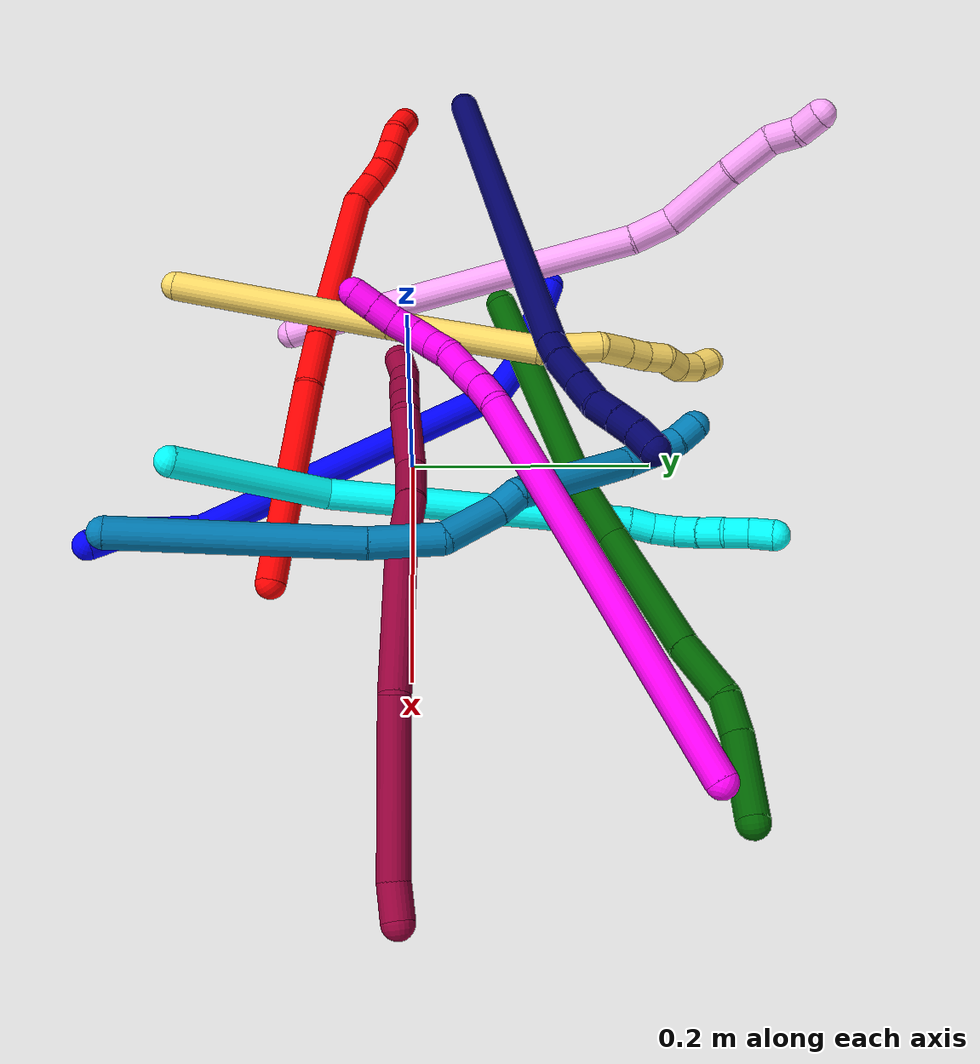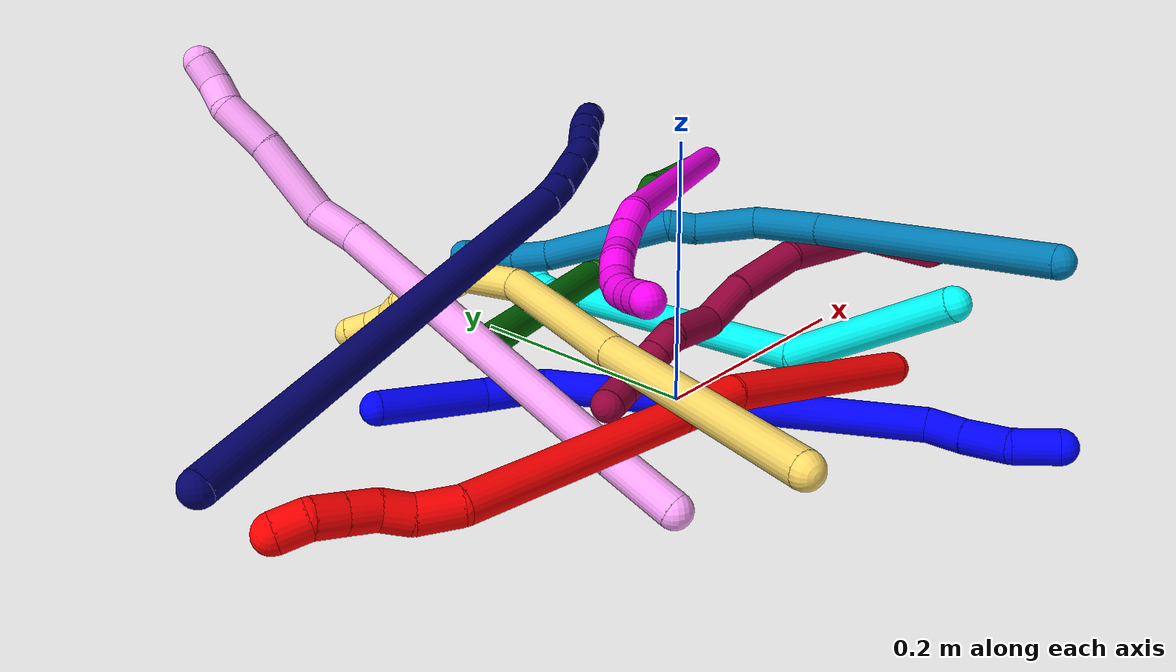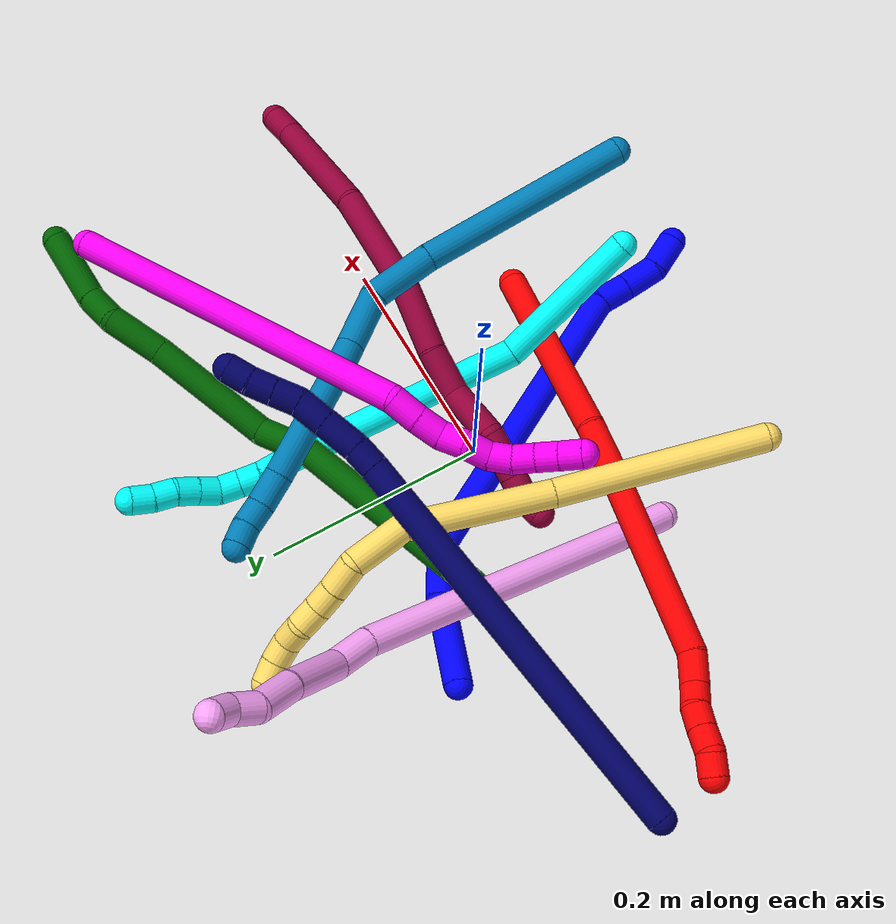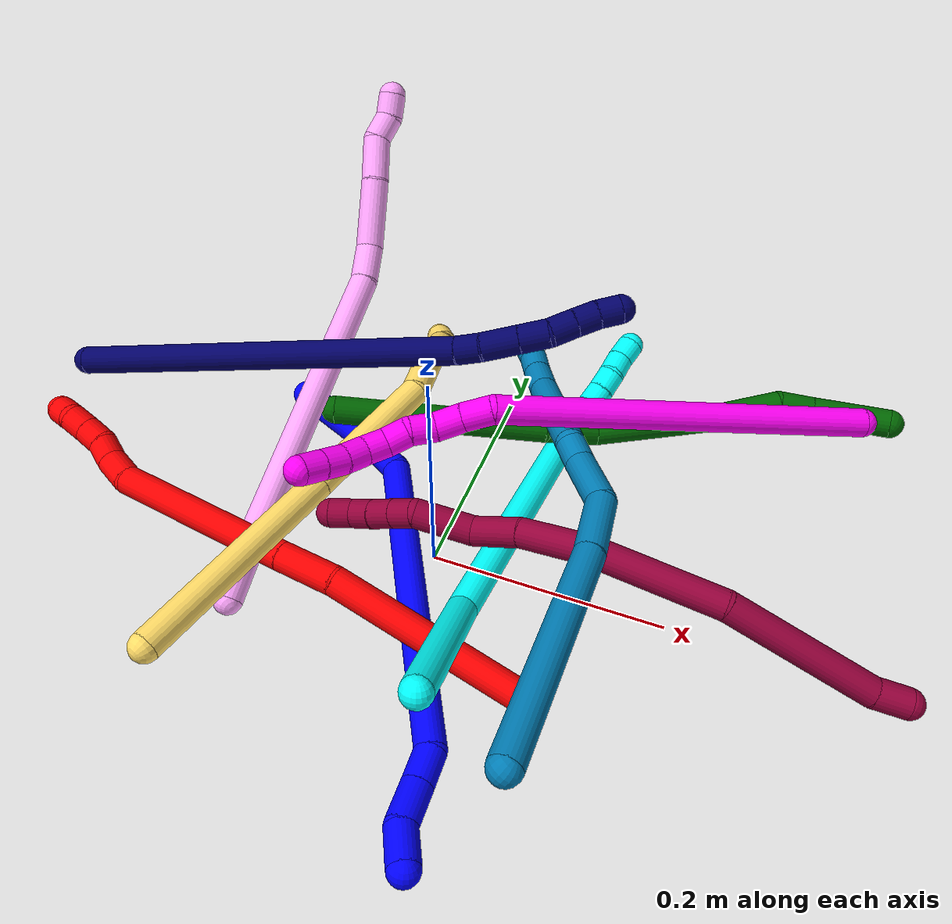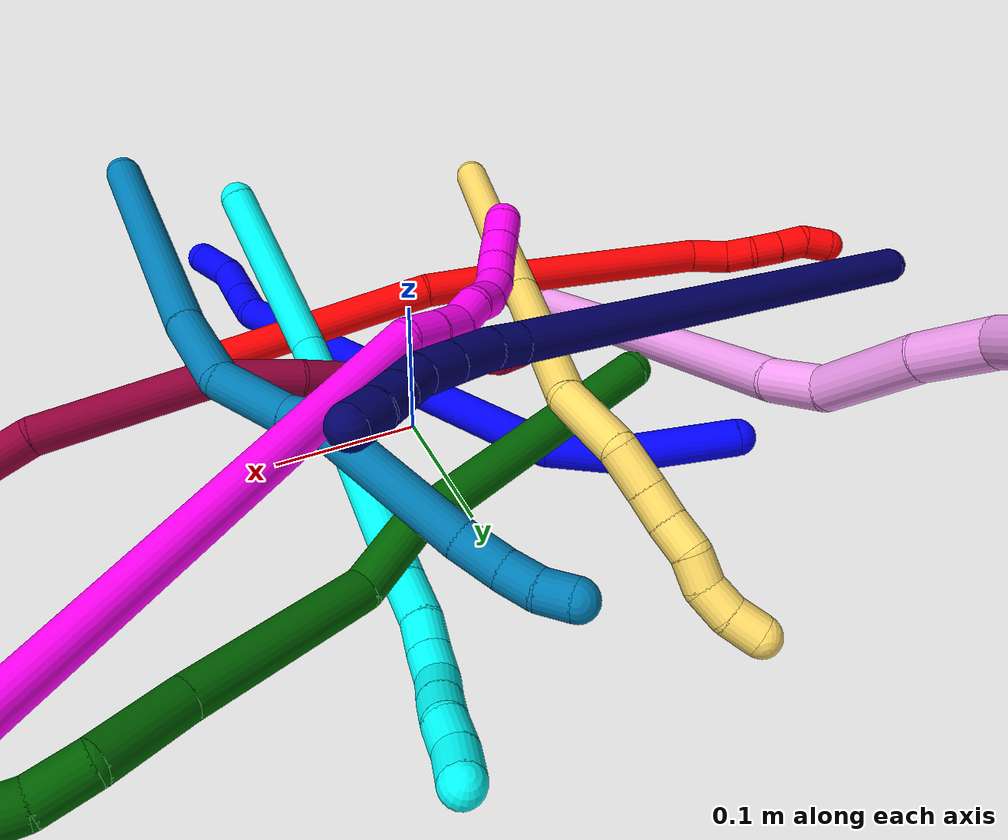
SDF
<sdf version="1.7">
 <world name="default">
  <plugin name="TubeGeneratorPlugin" filename="libtube_generator_plugin.so"/>
  <model name="photoneo_s_sensor">
   <static>1</static>
   <pose>0 0 2 1.57079 1.57079 3.14159</pose>
   <link name="link">
    <inertial><mass>0.1</mass></inertial>
    <sensor name="sensor" type="depth">
     <update_rate>30</update_rate>
     <camera>
      <horizontal_fov>1.22</horizontal_fov>
      <image><width>1920</width><height>1200</height><format>B8G8R8</format></image>
      <clip><near>0.1</near><far>2</far></clip>
      <depth_camera><output>points</output></depth_camera>
     </camera>
     <plugin name="camera_plugin" filename="libgazebo_ros_depth_camera.so">
      <baseline>0.2</baseline>
      <alwaysOn>1</alwaysOn>
      <updateRate>0.0</updateRate>
      <cameraName>camera_ir</cameraName>
      <imageTopicName>/camera/color/image_raw</imageTopicName>
      <cameraInfoTopicName>/camera/color/camera_info</cameraInfoTopicName>
      <depthImageTopicName>/camera/depth/image_raw</depthImageTopicName>
      <depthImageCameraInfoTopicName>/camera/depth/camera_info</depthImageCameraInfoTopicName>
      <pointCloudTopicName>/camera/depth/points</pointCloudTopicName>
      <frameName>fr_optical</frameName>
      <pointCloudCutoff>0.1</pointCloudCutoff>
      <pointCloudCutoffMax>2.0</pointCloudCutoffMax>
      <distortionK1>0</distortionK1>
      <distortionK2>0</distortionK2>
      <distortionK3>0</distortionK3>
      <distortionT1>0</distortionT1>
      <distortionT2>0</distortionT2>
      <CxPrime>0</CxPrime>
      <Cx>0</Cx>
      <Cy>0</Cy>
      <focalLength>0</focalLength>
      <hackBaseline>0</hackBaseline>
     </plugin>
    </sensor>
   </link>
  </model>
  <gravity>0 0 -9.8</gravity>
  <magnetic_field>6e-06 2.3e-05 -4.2e-05</magnetic_field>
  <atmosphere type="adiabatic"/>
  <physics name="default_physics" default="0" type="ode">
   <max_step_size>0.003</max_step_size>
   <real_time_factor>1</real_time_factor>
   <real_time_update_rate>1000</real_time_update_rate>
   <max_contacts>10000</max_contacts>
   <ode>
    <solver>
     <type>quick</type>
     <iters>100</iters>
     <sor>1.3</sor>
     <use_dynamic_moi_rescaling>0</use_dynamic_moi_rescaling>
    </solver>
    <constraints>
     <contact_max_correcting_vel>0</contact_max_correcting_vel>
     <contact_surface_layer>0.001</contact_surface_layer>
     <cfm>0</cfm>
     <erp>0.2</erp>
    </constraints>
   </ode>
  </physics>
  <scene><ambient>0.4 0.4 0.4 1</ambient><background>0.7 0.7 0.7 1</background><shadows>0</shadows></scene>
  <audio><device>default</device></audio>
  <spherical_coordinates>
   <surface_model>EARTH_WGS84</surface_model>
   <latitude_deg>0</latitude_deg>
   <longitude_deg>0</longitude_deg>
   <elevation>0</elevation>
   <heading_deg>0</heading_deg>
  </spherical_coordinates>
  <model name="bin">
   <static>1</static>
   <link name="bottom">
    <collision name="collision-bottom">
     <pose>0 0 -0.01 0 -0 0</pose>
     <geometry><box><size>0.8 0.6 0.02</size></box></geometry>
     <surface>
      <friction><ode><mu>100</mu><mu2>100</mu2></ode></friction>
      <contact><collide_bitmask>65535</collide_bitmask></contact>
     </surface>
    </collision>
   </link>
   <link name="west_wall">
    <collision name="collision-west_wall">
     <pose>-0.41 0 0.1 0 -0 0</pose>
     <geometry><box><size>0.02 0.6 0.2</size></box></geometry>
     <surface>
      <friction><ode><mu>100</mu><mu2>100</mu2></ode></friction>
      <contact><collide_bitmask>65535</collide_bitmask></contact>
     </surface>
    </collision>
   </link>
   <link name="east_wall">
    <collision name="collision-east_wall">
     <pose>0.41 0 0.1 0 -0 0</pose>
     <geometry><box><size>0.02 0.6 0.2</size></box></geometry>
     <surface>
      <friction><ode><mu>100</mu><mu2>100</mu2></ode></friction>
      <contact><collide_bitmask>65535</collide_bitmask></contact>
     </surface>
    </collision>
   </link>
   <link name="south_wall">
    <collision name="collision-south_wall">
     <pose>0 -0.31 0.1 0 -0 0</pose>
     <geometry><box><size>0.8 0.02 0.2</size></box></geometry>
     <surface>
      <friction><ode><mu>100</mu><mu2>100</mu2></ode></friction>
      <contact><collide_bitmask>65535</collide_bitmask></contact>
     </surface>
    </collision>
   </link>
   <link name="north_wall">
    <collision name="collision-north_wall">
     <pose>0 0.31 0.1 0 -0 0</pose>
     <geometry><box><size>0.8 0.02 0.2</size></box></geometry>
     <surface>
      <friction><ode><mu>100</mu><mu2>100</mu2></ode></friction>
      <contact><collide_bitmask>65535</collide_bitmask></contact>
     </surface>
    </collision>
   </link>
  </model>
  <model name="1">
   <static>0</static>
   <link name="1">
    <collision name="collision-cylinder-e_1_1_4">
     <pose>-0.023151 -0.032304 0.009598 1.28199 -0.601932 -0.455141</pose>
     <geometry><cylinder><radius>0.0125</radius><length>0.08177</length></cylinder></geometry>
     <surface>
      <friction><ode><mu>1.16</mu><mu2>1.16</mu2><slip1>0</slip1><slip2>0</slip2></ode></friction>
      <contact><ode><kp>1e+06</kp><kd>1</kd><max_vel>0</max_vel><min_depth>0.001</min_depth></ode></contact>
     </surface>
    </collision>
    <visual name="visual-cylinder-e_1_1_4">
     <pose>-0.023151 -0.032304 0.009598 1.28199 -0.601932 -0.455141</pose>
     <geometry><cylinder><radius>0.0125</radius><length>0.08177</length></cylinder></geometry>
     <material><ambient>0 0 1 1</ambient></material>
    </visual>
    <collision name="collision-cylinder-e_2_4_5">
     <pose>-0.054842 -0.085975 0.023055 1.3921 -0.374749 -0.314231</pose>
     <geometry><cylinder><radius>0.0125</radius><length>0.046667</length></cylinder></geometry>
     <surface>
      <friction><ode><mu>1.16</mu><mu2>1.16</mu2><slip1>0</slip1><slip2>0</slip2></ode></friction>
      <contact><ode><kp>1e+06</kp><kd>1</kd><max_vel>0</max_vel><min_depth>0.001</min_depth></ode></contact>
     </surface>
    </collision>
    <visual name="visual-cylinder-e_2_4_5">
     <pose>-0.054842 -0.085975 0.023055 1.3921 -0.374749 -0.314231</pose>
     <geometry><cylinder><radius>0.0125</radius><length>0.046667</length></cylinder></geometry>
     <material><ambient>0 0 1 1</ambient></material>
    </visual>
    <collision name="collision-cylinder-e_3_5_6">
     <pose>-0.045287 -0.239347 0.068467 1.26584 0.130026 0.095449</pose>
     <geometry><cylinder><radius>0.0125</radius><length>0.279134</length></cylinder></geometry>
     <surface>
      <friction><ode><mu>1.16</mu><mu2>1.16</mu2><slip1>0</slip1><slip2>0</slip2></ode></friction>
      <contact><ode><kp>1e+06</kp><kd>1</kd><max_vel>0</max_vel><min_depth>0.001</min_depth></ode></contact>
     </surface>
    </collision>
    <visual name="visual-cylinder-e_3_5_6">
     <pose>-0.045287 -0.239347 0.068467 1.26584 0.130026 0.095449</pose>
     <geometry><cylinder><radius>0.0125</radius><length>0.279134</length></cylinder></geometry>
     <material><ambient>0 0 1 1</ambient></material>
    </visual>
    <collision name="collision-cylinder-e_4_6_7">
     <pose>-0.019463 -0.382141 0.114496 1.17749 0.584415 0.396462</pose>
     <geometry><cylinder><radius>0.0125</radius><length>0.028013</length></cylinder></geometry>
     <surface>
      <friction><ode><mu>1.16</mu><mu2>1.16</mu2><slip1>0</slip1><slip2>0</slip2></ode></friction>
      <contact><ode><kp>1e+06</kp><kd>1</kd><max_vel>0</max_vel><min_depth>0.001</min_depth></ode></contact>
     </surface>
    </collision>
    <visual name="visual-cylinder-e_4_6_7">
     <pose>-0.019463 -0.382141 0.114496 1.17749 0.584415 0.396462</pose>
     <geometry><cylinder><radius>0.0125</radius><length>0.028013</length></cylinder></geometry>
     <material><ambient>0 0 1 1</ambient></material>
    </visual>
    <collision name="collision-cylinder-e_5_7_8">
     <pose>-0.002573 -0.406046 0.122615 1.29996 0.592479 0.455975</pose>
     <geometry><cylinder><radius>0.0125</radius><length>0.032815</length></cylinder></geometry>
     <surface>
      <friction><ode><mu>1.16</mu><mu2>1.16</mu2><slip1>0</slip1><slip2>0</slip2></ode></friction>
      <contact><ode><kp>1e+06</kp><kd>1</kd><max_vel>0</max_vel><min_depth>0.001</min_depth></ode></contact>
     </surface>
    </collision>
    <visual name="visual-cylinder-e_5_7_8">
     <pose>-0.002573 -0.406046 0.122615 1.29996 0.592479 0.455975</pose>
     <geometry><cylinder><radius>0.0125</radius><length>0.032815</length></cylinder></geometry>
     <material><ambient>0 0 1 1</ambient></material>
    </visual>
    <collision name="collision-cylinder-e_6_8_2">
     <pose>0.00938 -0.434434 0.129185 1.38135 0.177514 0.146833</pose>
     <geometry><cylinder><radius>0.0125</radius><length>0.0316</length></cylinder></geometry>
     <surface>
      <friction><ode><mu>1.16</mu><mu2>1.16</mu2><slip1>0</slip1><slip2>0</slip2></ode></friction>
      <contact><ode><kp>1e+06</kp><kd>1</kd><max_vel>0</max_vel><min_depth>0.001</min_depth></ode></contact>
     </surface>
    </collision>
    <visual name="visual-cylinder-e_6_8_2">
     <pose>0.00938 -0.434434 0.129185 1.38135 0.177514 0.146833</pose>
     <geometry><cylinder><radius>0.0125</radius><length>0.0316</length></cylinder></geometry>
     <material><ambient>0 0 1 1</ambient></material>
    </visual>
    <collision name="collision-sphere-2">
     <pose>0.01217 -0.449708 0.132113 0 -0 0</pose>
     <geometry><sphere><radius>0.0125</radius></sphere></geometry>
     <surface>
      <friction><ode><mu>1.16</mu><mu2>1.16</mu2><slip1>0</slip1><slip2>0</slip2></ode></friction>
      <contact><ode><kp>1e+06</kp><kd>1</kd><max_vel>0</max_vel><min_depth>0.001</min_depth></ode></contact>
     </surface>
    </collision>
    <visual name="visual-sphere-2">
     <pose>0.01217 -0.449708 0.132113 0 -0 0</pose>
     <geometry><sphere><radius>0.0125</radius></sphere></geometry>
     <material><ambient>0 0 1 1</ambient></material>
    </visual>
    <collision name="collision-sphere-4">
     <pose>-0.046301 -0.064607 0.019196 0 -0 0</pose>
     <geometry><sphere><radius>0.0125</radius></sphere></geometry>
     <surface>
      <friction><ode><mu>1.16</mu><mu2>1.16</mu2><slip1>0</slip1><slip2>0</slip2></ode></friction>
      <contact><ode><kp>1e+06</kp><kd>1</kd><max_vel>0</max_vel><min_depth>0.001</min_depth></ode></contact>
     </surface>
    </collision>
    <visual name="visual-sphere-4">
     <pose>-0.046301 -0.064607 0.019196 0 -0 0</pose>
     <geometry><sphere><radius>0.0125</radius></sphere></geometry>
     <material><ambient>0 0 1 1</ambient></material>
    </visual>
    <collision name="collision-sphere-1">
     <geometry><sphere><radius>0.0125</radius></sphere></geometry>
     <surface>
      <friction><ode><mu>1.16</mu><mu2>1.16</mu2><slip1>0</slip1><slip2>0</slip2></ode></friction>
      <contact><ode><kp>1e+06</kp><kd>1</kd><max_vel>0</max_vel><min_depth>0.001</min_depth></ode></contact>
     </surface>
    </collision>
    <visual name="visual-sphere-1">
     <geometry><sphere><radius>0.0125</radius></sphere></geometry>
     <material><ambient>0 0 1 1</ambient></material>
    </visual>
    <collision name="collision-sphere-8">
     <pose>0.00659 -0.419161 0.126256 0 -0 0</pose>
     <geometry><sphere><radius>0.0125</radius></sphere></geometry>
     <surface>
      <friction><ode><mu>1.16</mu><mu2>1.16</mu2><slip1>0</slip1><slip2>0</slip2></ode></friction>
      <contact><ode><kp>1e+06</kp><kd>1</kd><max_vel>0</max_vel><min_depth>0.001</min_depth></ode></contact>
     </surface>
    </collision>
    <visual name="visual-sphere-8">
     <pose>0.00659 -0.419161 0.126256 0 -0 0</pose>
     <geometry><sphere><radius>0.0125</radius></sphere></geometry>
     <material><ambient>0 0 1 1</ambient></material>
    </visual>
    <collision name="collision-sphere-5">
     <pose>-0.063383 -0.107344 0.026915 0 -0 0</pose>
     <geometry><sphere><radius>0.0125</radius></sphere></geometry>
     <surface>
      <friction><ode><mu>1.16</mu><mu2>1.16</mu2><slip1>0</slip1><slip2>0</slip2></ode></friction>
      <contact><ode><kp>1e+06</kp><kd>1</kd><max_vel>0</max_vel><min_depth>0.001</min_depth></ode></contact>
     </surface>
    </collision>
    <visual name="visual-sphere-5">
     <pose>-0.063383 -0.107344 0.026915 0 -0 0</pose>
     <geometry><sphere><radius>0.0125</radius></sphere></geometry>
     <material><ambient>0 0 1 1</ambient></material>
    </visual>
    <collision name="collision-sphere-6">
     <pose>-0.02719 -0.371351 0.110019 0 -0 0</pose>
     <geometry><sphere><radius>0.0125</radius></sphere></geometry>
     <surface>
      <friction><ode><mu>1.16</mu><mu2>1.16</mu2><slip1>0</slip1><slip2>0</slip2></ode></friction>
      <contact><ode><kp>1e+06</kp><kd>1</kd><max_vel>0</max_vel><min_depth>0.001</min_depth></ode></contact>
     </surface>
    </collision>
    <visual name="visual-sphere-6">
     <pose>-0.02719 -0.371351 0.110019 0 -0 0</pose>
     <geometry><sphere><radius>0.0125</radius></sphere></geometry>
     <material><ambient>0 0 1 1</ambient></material>
    </visual>
    <collision name="collision-sphere-7">
     <pose>-0.011735 -0.392931 0.118973 0 -0 0</pose>
     <geometry><sphere><radius>0.0125</radius></sphere></geometry>
     <surface>
      <friction><ode><mu>1.16</mu><mu2>1.16</mu2><slip1>0</slip1><slip2>0</slip2></ode></friction>
      <contact><ode><kp>1e+06</kp><kd>1</kd><max_vel>0</max_vel><min_depth>0.001</min_depth></ode></contact>
     </surface>
    </collision>
    <visual name="visual-sphere-7">
     <pose>-0.011735 -0.392931 0.118973 0 -0 0</pose>
     <geometry><sphere><radius>0.0125</radius></sphere></geometry>
     <material><ambient>0 0 1 1</ambient></material>
    </visual>
    <inertial>
     <pose>-0.034853 -0.222443 0.064571 0 -0 0</pose>
     <mass>0.5</mass>
     <inertia>
      <ixx>0.00201</ixx>
      <ixy>0</ixy>
      <ixz>0</ixz>
      <iyy>0.000717</iyy>
      <iyz>0</iyz>
      <izz>0.001582</izz>
     </inertia>
    </inertial>
   </link>
   <pose>-0.183529 0.123647 0.021272 -2.86568 -0.191392 -2.50326</pose>
  </model>
  <model name="2">
   <static>0</static>
   <link name="2">
    <collision name="collision-cylinder-e_1_1_4">
     <pose>-0.071743 -0.019403 0.045704 0.401486 -0.965406 -0.212469</pose>
     <geometry><cylinder><radius>0.0125</radius><length>0.174499</length></cylinder></geometry>
     <surface>
      <friction><ode><mu>1.16</mu><mu2>1.16</mu2><slip1>0</slip1><slip2>0</slip2></ode></friction>
      <contact><ode><kp>1e+06</kp><kd>1</kd><max_vel>0</max_vel><min_depth>0.001</min_depth></ode></contact>
     </surface>
    </collision>
    <visual name="visual-cylinder-e_1_1_4">
     <pose>-0.071743 -0.019403 0.045704 0.401486 -0.965406 -0.212469</pose>
     <geometry><cylinder><radius>0.0125</radius><length>0.174499</length></cylinder></geometry>
     <material><ambient>1 0 0 1</ambient></material>
    </visual>
    <collision name="collision-cylinder-e_2_4_5">
     <pose>-0.164236 -0.048469 0.101651 0.756243 -0.97455 -0.414928</pose>
     <geometry><cylinder><radius>0.0125</radius><length>0.050152</length></cylinder></geometry>
     <surface>
      <friction><ode><mu>1.16</mu><mu2>1.16</mu2><slip1>0</slip1><slip2>0</slip2></ode></friction>
      <contact><ode><kp>1e+06</kp><kd>1</kd><max_vel>0</max_vel><min_depth>0.001</min_depth></ode></contact>
     </surface>
    </collision>
    <visual name="visual-cylinder-e_2_4_5">
     <pose>-0.164236 -0.048469 0.101651 0.756243 -0.97455 -0.414928</pose>
     <geometry><cylinder><radius>0.0125</radius><length>0.050152</length></cylinder></geometry>
     <material><ambient>1 0 0 1</ambient></material>
    </visual>
    <collision name="collision-cylinder-e_3_5_6">
     <pose>-0.255069 -0.08991 0.143219 0.792581 -1.00384 -0.451436</pose>
     <geometry><cylinder><radius>0.0125</radius><length>0.166167</length></cylinder></geometry>
     <surface>
      <friction><ode><mu>1.16</mu><mu2>1.16</mu2><slip1>0</slip1><slip2>0</slip2></ode></friction>
      <contact><ode><kp>1e+06</kp><kd>1</kd><max_vel>0</max_vel><min_depth>0.001</min_depth></ode></contact>
     </surface>
    </collision>
    <visual name="visual-cylinder-e_3_5_6">
     <pose>-0.255069 -0.08991 0.143219 0.792581 -1.00384 -0.451436</pose>
     <geometry><cylinder><radius>0.0125</radius><length>0.166167</length></cylinder></geometry>
     <material><ambient>1 0 0 1</ambient></material>
    </visual>
    <collision name="collision-cylinder-e_4_6_7">
     <pose>-0.339154 -0.12413 0.176863 0.811052 -1.3347 -0.652401</pose>
     <geometry><cylinder><radius>0.0125</radius><length>0.0288</length></cylinder></geometry>
     <surface>
      <friction><ode><mu>1.16</mu><mu2>1.16</mu2><slip1>0</slip1><slip2>0</slip2></ode></friction>
      <contact><ode><kp>1e+06</kp><kd>1</kd><max_vel>0</max_vel><min_depth>0.001</min_depth></ode></contact>
     </surface>
    </collision>
    <visual name="visual-cylinder-e_4_6_7">
     <pose>-0.339154 -0.12413 0.176863 0.811052 -1.3347 -0.652401</pose>
     <geometry><cylinder><radius>0.0125</radius><length>0.0288</length></cylinder></geometry>
     <material><ambient>1 0 0 1</ambient></material>
    </visual>
    <collision name="collision-cylinder-e_5_7_8">
     <pose>-0.362784 -0.125233 0.182002 -0.443393 -1.25739 0.324898</pose>
     <geometry><cylinder><radius>0.0125</radius><length>0.020245</length></cylinder></geometry>
     <surface>
      <friction><ode><mu>1.16</mu><mu2>1.16</mu2><slip1>0</slip1><slip2>0</slip2></ode></friction>
      <contact><ode><kp>1e+06</kp><kd>1</kd><max_vel>0</max_vel><min_depth>0.001</min_depth></ode></contact>
     </surface>
    </collision>
    <visual name="visual-cylinder-e_5_7_8">
     <pose>-0.362784 -0.125233 0.182002 -0.443393 -1.25739 0.324898</pose>
     <geometry><cylinder><radius>0.0125</radius><length>0.020245</length></cylinder></geometry>
     <material><ambient>1 0 0 1</ambient></material>
    </visual>
    <collision name="collision-cylinder-e_6_8_9">
     <pose>-0.381548 -0.125429 0.18874 0.373136 -1.13915 -0.240588</pose>
     <geometry><cylinder><radius>0.0125</radius><length>0.020116</length></cylinder></geometry>
     <surface>
      <friction><ode><mu>1.16</mu><mu2>1.16</mu2><slip1>0</slip1><slip2>0</slip2></ode></friction>
      <contact><ode><kp>1e+06</kp><kd>1</kd><max_vel>0</max_vel><min_depth>0.001</min_depth></ode></contact>
     </surface>
    </collision>
    <visual name="visual-cylinder-e_6_8_9">
     <pose>-0.381548 -0.125429 0.18874 0.373136 -1.13915 -0.240588</pose>
     <geometry><cylinder><radius>0.0125</radius><length>0.020116</length></cylinder></geometry>
     <material><ambient>1 0 0 1</ambient></material>
    </visual>
    <collision name="collision-cylinder-e_7_9_10">
     <pose>-0.399549 -0.128591 0.196999 0.358864 -1.08893 -0.218784</pose>
     <geometry><cylinder><radius>0.0125</radius><length>0.020008</length></cylinder></geometry>
     <surface>
      <friction><ode><mu>1.16</mu><mu2>1.16</mu2><slip1>0</slip1><slip2>0</slip2></ode></friction>
      <contact><ode><kp>1e+06</kp><kd>1</kd><max_vel>0</max_vel><min_depth>0.001</min_depth></ode></contact>
     </surface>
    </collision>
    <visual name="visual-cylinder-e_7_9_10">
     <pose>-0.399549 -0.128591 0.196999 0.358864 -1.08893 -0.218784</pose>
     <geometry><cylinder><radius>0.0125</radius><length>0.020008</length></cylinder></geometry>
     <material><ambient>1 0 0 1</ambient></material>
    </visual>
    <collision name="collision-cylinder-e_8_10_2">
     <pose>-0.417678 -0.133895 0.202224 1.33468 -1.1833 -0.973857</pose>
     <geometry><cylinder><radius>0.0125</radius><length>0.020013</length></cylinder></geometry>
     <surface>
      <friction><ode><mu>1.16</mu><mu2>1.16</mu2><slip1>0</slip1><slip2>0</slip2></ode></friction>
      <contact><ode><kp>1e+06</kp><kd>1</kd><max_vel>0</max_vel><min_depth>0.001</min_depth></ode></contact>
     </surface>
    </collision>
    <visual name="visual-cylinder-e_8_10_2">
     <pose>-0.417678 -0.133895 0.202224 1.33468 -1.1833 -0.973857</pose>
     <geometry><cylinder><radius>0.0125</radius><length>0.020013</length></cylinder></geometry>
     <material><ambient>1 0 0 1</ambient></material>
    </visual>
    <collision name="collision-sphere-2">
     <pose>-0.426943 -0.137572 0.203109 0 -0 0</pose>
     <geometry><sphere><radius>0.0125</radius></sphere></geometry>
     <surface>
      <friction><ode><mu>1.16</mu><mu2>1.16</mu2><slip1>0</slip1><slip2>0</slip2></ode></friction>
      <contact><ode><kp>1e+06</kp><kd>1</kd><max_vel>0</max_vel><min_depth>0.001</min_depth></ode></contact>
     </surface>
    </collision>
    <visual name="visual-sphere-2">
     <pose>-0.426943 -0.137572 0.203109 0 -0 0</pose>
     <geometry><sphere><radius>0.0125</radius></sphere></geometry>
     <material><ambient>1 0 0 1</ambient></material>
    </visual>
    <collision name="collision-sphere-10">
     <pose>-0.408414 -0.130219 0.20134 0 -0 0</pose>
     <geometry><sphere><radius>0.0125</radius></sphere></geometry>
     <surface>
      <friction><ode><mu>1.16</mu><mu2>1.16</mu2><slip1>0</slip1><slip2>0</slip2></ode></friction>
      <contact><ode><kp>1e+06</kp><kd>1</kd><max_vel>0</max_vel><min_depth>0.001</min_depth></ode></contact>
     </surface>
    </collision>
    <visual name="visual-sphere-10">
     <pose>-0.408414 -0.130219 0.20134 0 -0 0</pose>
     <geometry><sphere><radius>0.0125</radius></sphere></geometry>
     <material><ambient>1 0 0 1</ambient></material>
    </visual>
    <collision name="collision-sphere-9">
     <pose>-0.390684 -0.126963 0.192658 0 -0 0</pose>
     <geometry><sphere><radius>0.0125</radius></sphere></geometry>
     <surface>
      <friction><ode><mu>1.16</mu><mu2>1.16</mu2><slip1>0</slip1><slip2>0</slip2></ode></friction>
      <contact><ode><kp>1e+06</kp><kd>1</kd><max_vel>0</max_vel><min_depth>0.001</min_depth></ode></contact>
     </surface>
    </collision>
    <visual name="visual-sphere-9">
     <pose>-0.390684 -0.126963 0.192658 0 -0 0</pose>
     <geometry><sphere><radius>0.0125</radius></sphere></geometry>
     <material><ambient>1 0 0 1</ambient></material>
    </visual>
    <collision name="collision-sphere-4">
     <pose>-0.143487 -0.038807 0.091408 0 -0 0</pose>
     <geometry><sphere><radius>0.0125</radius></sphere></geometry>
     <surface>
      <friction><ode><mu>1.16</mu><mu2>1.16</mu2><slip1>0</slip1><slip2>0</slip2></ode></friction>
      <contact><ode><kp>1e+06</kp><kd>1</kd><max_vel>0</max_vel><min_depth>0.001</min_depth></ode></contact>
     </surface>
    </collision>
    <visual name="visual-sphere-4">
     <pose>-0.143487 -0.038807 0.091408 0 -0 0</pose>
     <geometry><sphere><radius>0.0125</radius></sphere></geometry>
     <material><ambient>1 0 0 1</ambient></material>
    </visual>
    <collision name="collision-sphere-1">
     <geometry><sphere><radius>0.0125</radius></sphere></geometry>
     <surface>
      <friction><ode><mu>1.16</mu><mu2>1.16</mu2><slip1>0</slip1><slip2>0</slip2></ode></friction>
      <contact><ode><kp>1e+06</kp><kd>1</kd><max_vel>0</max_vel><min_depth>0.001</min_depth></ode></contact>
     </surface>
    </collision>
    <visual name="visual-sphere-1">
     <geometry><sphere><radius>0.0125</radius></sphere></geometry>
     <material><ambient>1 0 0 1</ambient></material>
    </visual>
    <collision name="collision-sphere-8">
     <pose>-0.372413 -0.123895 0.184821 0 -0 0</pose>
     <geometry><sphere><radius>0.0125</radius></sphere></geometry>
     <surface>
      <friction><ode><mu>1.16</mu><mu2>1.16</mu2><slip1>0</slip1><slip2>0</slip2></ode></friction>
      <contact><ode><kp>1e+06</kp><kd>1</kd><max_vel>0</max_vel><min_depth>0.001</min_depth></ode></contact>
     </surface>
    </collision>
    <visual name="visual-sphere-8">
     <pose>-0.372413 -0.123895 0.184821 0 -0 0</pose>
     <geometry><sphere><radius>0.0125</radius></sphere></geometry>
     <material><ambient>1 0 0 1</ambient></material>
    </visual>
    <collision name="collision-sphere-5">
     <pose>-0.184985 -0.058132 0.111894 0 -0 0</pose>
     <geometry><sphere><radius>0.0125</radius></sphere></geometry>
     <surface>
      <friction><ode><mu>1.16</mu><mu2>1.16</mu2><slip1>0</slip1><slip2>0</slip2></ode></friction>
      <contact><ode><kp>1e+06</kp><kd>1</kd><max_vel>0</max_vel><min_depth>0.001</min_depth></ode></contact>
     </surface>
    </collision>
    <visual name="visual-sphere-5">
     <pose>-0.184985 -0.058132 0.111894 0 -0 0</pose>
     <geometry><sphere><radius>0.0125</radius></sphere></geometry>
     <material><ambient>1 0 0 1</ambient></material>
    </visual>
    <collision name="collision-sphere-6">
     <pose>-0.325153 -0.121688 0.174544 0 -0 0</pose>
     <geometry><sphere><radius>0.0125</radius></sphere></geometry>
     <surface>
      <friction><ode><mu>1.16</mu><mu2>1.16</mu2><slip1>0</slip1><slip2>0</slip2></ode></friction>
      <contact><ode><kp>1e+06</kp><kd>1</kd><max_vel>0</max_vel><min_depth>0.001</min_depth></ode></contact>
     </surface>
    </collision>
    <visual name="visual-sphere-6">
     <pose>-0.325153 -0.121688 0.174544 0 -0 0</pose>
     <geometry><sphere><radius>0.0125</radius></sphere></geometry>
     <material><ambient>1 0 0 1</ambient></material>
    </visual>
    <collision name="collision-sphere-7">
     <pose>-0.353155 -0.126572 0.179183 0 -0 0</pose>
     <geometry><sphere><radius>0.0125</radius></sphere></geometry>
     <surface>
      <friction><ode><mu>1.16</mu><mu2>1.16</mu2><slip1>0</slip1><slip2>0</slip2></ode></friction>
      <contact><ode><kp>1e+06</kp><kd>1</kd><max_vel>0</max_vel><min_depth>0.001</min_depth></ode></contact>
     </surface>
    </collision>
    <visual name="visual-sphere-7">
     <pose>-0.353155 -0.126572 0.179183 0 -0 0</pose>
     <geometry><sphere><radius>0.0125</radius></sphere></geometry>
     <material><ambient>1 0 0 1</ambient></material>
    </visual>
    <inertial>
     <pose>-0.208561 -0.069285 0.11487 0 -0 0</pose>
     <mass>0.5</mass>
     <inertia>
      <ixx>0.000265</ixx>
      <ixy>0</ixy>
      <ixz>0</ixz>
      <iyy>0.000643</iyy>
      <iyz>0</iyz>
      <izz>0.000987</izz>
     </inertia>
    </inertial>
   </link>
   <pose>0.1214 -0.111705 0.016989 0.851745 0.026877 -0.733992</pose>
  </model>
  <model name="3">
   <static>0</static>
   <link name="3">
    <collision name="collision-cylinder-e_1_1_4">
     <pose>0.025309 0.06113 0.012876 -1.3632 0.384919 -0.313607</pose>
     <geometry><cylinder><radius>0.0125</radius><length>0.134806</length></cylinder></geometry>
     <surface>
      <friction><ode><mu>1.16</mu><mu2>1.16</mu2><slip1>0</slip1><slip2>0</slip2></ode></friction>
      <contact><ode><kp>1e+06</kp><kd>1</kd><max_vel>0</max_vel><min_depth>0.001</min_depth></ode></contact>
     </surface>
    </collision>
    <visual name="visual-cylinder-e_1_1_4">
     <pose>0.025309 0.06113 0.012876 -1.3632 0.384919 -0.313607</pose>
     <geometry><cylinder><radius>0.0125</radius><length>0.134806</length></cylinder></geometry>
     <material><ambient>0.003922 1 0.996078 1</ambient></material>
    </visual>
    <collision name="collision-cylinder-e_2_4_5">
     <pose>0.07004 0.226591 0.000896 -1.80467 0.179153 -0.226483</pose>
     <geometry><cylinder><radius>0.0125</radius><length>0.217991</length></cylinder></geometry>
     <surface>
      <friction><ode><mu>1.16</mu><mu2>1.16</mu2><slip1>0</slip1><slip2>0</slip2></ode></friction>
      <contact><ode><kp>1e+06</kp><kd>1</kd><max_vel>0</max_vel><min_depth>0.001</min_depth></ode></contact>
     </surface>
    </collision>
    <visual name="visual-cylinder-e_2_4_5">
     <pose>0.07004 0.226591 0.000896 -1.80467 0.179153 -0.226483</pose>
     <geometry><cylinder><radius>0.0125</radius><length>0.217991</length></cylinder></geometry>
     <material><ambient>0.003922 1 0.996078 1</ambient></material>
    </visual>
    <collision name="collision-cylinder-e_3_5_6">
     <pose>0.092495 0.34393 -0.026343 -1.7521 0.225404 -0.26998</pose>
     <geometry><cylinder><radius>0.0125</radius><length>0.027135</length></cylinder></geometry>
     <surface>
      <friction><ode><mu>1.16</mu><mu2>1.16</mu2><slip1>0</slip1><slip2>0</slip2></ode></friction>
      <contact><ode><kp>1e+06</kp><kd>1</kd><max_vel>0</max_vel><min_depth>0.001</min_depth></ode></contact>
     </surface>
    </collision>
    <visual name="visual-cylinder-e_3_5_6">
     <pose>0.092495 0.34393 -0.026343 -1.7521 0.225404 -0.26998</pose>
     <geometry><cylinder><radius>0.0125</radius><length>0.027135</length></cylinder></geometry>
     <material><ambient>0.003922 1 0.996078 1</ambient></material>
    </visual>
    <collision name="collision-cylinder-e_4_6_7">
     <pose>0.096195 0.366852 -0.029933 -1.69173 0.066785 -0.075385</pose>
     <geometry><cylinder><radius>0.0125</radius><length>0.020021</length></cylinder></geometry>
     <surface>
      <friction><ode><mu>1.16</mu><mu2>1.16</mu2><slip1>0</slip1><slip2>0</slip2></ode></friction>
      <contact><ode><kp>1e+06</kp><kd>1</kd><max_vel>0</max_vel><min_depth>0.001</min_depth></ode></contact>
     </surface>
    </collision>
    <visual name="visual-cylinder-e_4_6_7">
     <pose>0.096195 0.366852 -0.029933 -1.69173 0.066785 -0.075385</pose>
     <geometry><cylinder><radius>0.0125</radius><length>0.020021</length></cylinder></geometry>
     <material><ambient>0.003922 1 0.996078 1</ambient></material>
    </visual>
    <collision name="collision-cylinder-e_5_7_8">
     <pose>0.097584 0.386288 -0.034114 -1.87377 0.072116 -0.098066</pose>
     <geometry><cylinder><radius>0.0125</radius><length>0.020002</length></cylinder></geometry>
     <surface>
      <friction><ode><mu>1.16</mu><mu2>1.16</mu2><slip1>0</slip1><slip2>0</slip2></ode></friction>
      <contact><ode><kp>1e+06</kp><kd>1</kd><max_vel>0</max_vel><min_depth>0.001</min_depth></ode></contact>
     </surface>
    </collision>
    <visual name="visual-cylinder-e_5_7_8">
     <pose>0.097584 0.386288 -0.034114 -1.87377 0.072116 -0.098066</pose>
     <geometry><cylinder><radius>0.0125</radius><length>0.020002</length></cylinder></geometry>
     <material><ambient>0.003922 1 0.996078 1</ambient></material>
    </visual>
    <collision name="collision-cylinder-e_6_8_9">
     <pose>0.096642 0.403481 -0.043291 -2.25055 -0.166929 0.346854</pose>
     <geometry><cylinder><radius>0.0125</radius><length>0.020009</length></cylinder></geometry>
     <surface>
      <friction><ode><mu>1.16</mu><mu2>1.16</mu2><slip1>0</slip1><slip2>0</slip2></ode></friction>
      <contact><ode><kp>1e+06</kp><kd>1</kd><max_vel>0</max_vel><min_depth>0.001</min_depth></ode></contact>
     </surface>
    </collision>
    <visual name="visual-cylinder-e_6_8_9">
     <pose>0.096642 0.403481 -0.043291 -2.25055 -0.166929 0.346854</pose>
     <geometry><cylinder><radius>0.0125</radius><length>0.020009</length></cylinder></geometry>
     <material><ambient>0.003922 1 0.996078 1</ambient></material>
    </visual>
    <collision name="collision-cylinder-e_7_9_10">
     <pose>0.09394 0.41886 -0.055803 -2.25696 -0.104011 0.218929</pose>
     <geometry><cylinder><radius>0.0125</radius><length>0.02003</length></cylinder></geometry>
     <surface>
      <friction><ode><mu>1.16</mu><mu2>1.16</mu2><slip1>0</slip1><slip2>0</slip2></ode></friction>
      <contact><ode><kp>1e+06</kp><kd>1</kd><max_vel>0</max_vel><min_depth>0.001</min_depth></ode></contact>
     </surface>
    </collision>
    <visual name="visual-cylinder-e_7_9_10">
     <pose>0.09394 0.41886 -0.055803 -2.25696 -0.104011 0.218929</pose>
     <geometry><cylinder><radius>0.0125</radius><length>0.02003</length></cylinder></geometry>
     <material><ambient>0.003922 1 0.996078 1</ambient></material>
    </visual>
    <collision name="collision-cylinder-e_8_10_11">
     <pose>0.093533 0.435383 -0.066795 -2.05881 0.063277 -0.105168</pose>
     <geometry><cylinder><radius>0.0125</radius><length>0.020005</length></cylinder></geometry>
     <surface>
      <friction><ode><mu>1.16</mu><mu2>1.16</mu2><slip1>0</slip1><slip2>0</slip2></ode></friction>
      <contact><ode><kp>1e+06</kp><kd>1</kd><max_vel>0</max_vel><min_depth>0.001</min_depth></ode></contact>
     </surface>
    </collision>
    <visual name="visual-cylinder-e_8_10_11">
     <pose>0.093533 0.435383 -0.066795 -2.05881 0.063277 -0.105168</pose>
     <geometry><cylinder><radius>0.0125</radius><length>0.020005</length></cylinder></geometry>
     <material><ambient>0.003922 1 0.996078 1</ambient></material>
    </visual>
    <collision name="collision-cylinder-e_9_11_2">
     <pose>0.09329 0.452741 -0.076606 -2.11175 -0.087708 0.154795</pose>
     <geometry><cylinder><radius>0.0125</radius><length>0.020002</length></cylinder></geometry>
     <surface>
      <friction><ode><mu>1.16</mu><mu2>1.16</mu2><slip1>0</slip1><slip2>0</slip2></ode></friction>
      <contact><ode><kp>1e+06</kp><kd>1</kd><max_vel>0</max_vel><min_depth>0.001</min_depth></ode></contact>
     </surface>
    </collision>
    <visual name="visual-cylinder-e_9_11_2">
     <pose>0.09329 0.452741 -0.076606 -2.11175 -0.087708 0.154795</pose>
     <geometry><cylinder><radius>0.0125</radius><length>0.020002</length></cylinder></geometry>
     <material><ambient>0.003922 1 0.996078 1</ambient></material>
    </visual>
    <collision name="collision-sphere-2">
     <pose>0.092414 0.461281 -0.081736 0 -0 0</pose>
     <geometry><sphere><radius>0.0125</radius></sphere></geometry>
     <surface>
      <friction><ode><mu>1.16</mu><mu2>1.16</mu2><slip1>0</slip1><slip2>0</slip2></ode></friction>
      <contact><ode><kp>1e+06</kp><kd>1</kd><max_vel>0</max_vel><min_depth>0.001</min_depth></ode></contact>
     </surface>
    </collision>
    <visual name="visual-sphere-2">
     <pose>0.092414 0.461281 -0.081736 0 -0 0</pose>
     <geometry><sphere><radius>0.0125</radius></sphere></geometry>
     <material><ambient>0.003922 1 0.996078 1</ambient></material>
    </visual>
    <collision name="collision-sphere-11">
     <pose>0.094166 0.4442 -0.071475 0 -0 0</pose>
     <geometry><sphere><radius>0.0125</radius></sphere></geometry>
     <surface>
      <friction><ode><mu>1.16</mu><mu2>1.16</mu2><slip1>0</slip1><slip2>0</slip2></ode></friction>
      <contact><ode><kp>1e+06</kp><kd>1</kd><max_vel>0</max_vel><min_depth>0.001</min_depth></ode></contact>
     </surface>
    </collision>
    <visual name="visual-sphere-11">
     <pose>0.094166 0.4442 -0.071475 0 -0 0</pose>
     <geometry><sphere><radius>0.0125</radius></sphere></geometry>
     <material><ambient>0.003922 1 0.996078 1</ambient></material>
    </visual>
    <collision name="collision-sphere-10">
     <pose>0.092901 0.426566 -0.062114 0 -0 0</pose>
     <geometry><sphere><radius>0.0125</radius></sphere></geometry>
     <surface>
      <friction><ode><mu>1.16</mu><mu2>1.16</mu2><slip1>0</slip1><slip2>0</slip2></ode></friction>
      <contact><ode><kp>1e+06</kp><kd>1</kd><max_vel>0</max_vel><min_depth>0.001</min_depth></ode></contact>
     </surface>
    </collision>
    <visual name="visual-sphere-10">
     <pose>0.092901 0.426566 -0.062114 0 -0 0</pose>
     <geometry><sphere><radius>0.0125</radius></sphere></geometry>
     <material><ambient>0.003922 1 0.996078 1</ambient></material>
    </visual>
    <collision name="collision-sphere-9">
     <pose>0.09498 0.411153 -0.049492 0 -0 0</pose>
     <geometry><sphere><radius>0.0125</radius></sphere></geometry>
     <surface>
      <friction><ode><mu>1.16</mu><mu2>1.16</mu2><slip1>0</slip1><slip2>0</slip2></ode></friction>
      <contact><ode><kp>1e+06</kp><kd>1</kd><max_vel>0</max_vel><min_depth>0.001</min_depth></ode></contact>
     </surface>
    </collision>
    <visual name="visual-sphere-9">
     <pose>0.09498 0.411153 -0.049492 0 -0 0</pose>
     <geometry><sphere><radius>0.0125</radius></sphere></geometry>
     <material><ambient>0.003922 1 0.996078 1</ambient></material>
    </visual>
    <collision name="collision-sphere-4">
     <pose>0.050618 0.12226 0.025752 0 -0 0</pose>
     <geometry><sphere><radius>0.0125</radius></sphere></geometry>
     <surface>
      <friction><ode><mu>1.16</mu><mu2>1.16</mu2><slip1>0</slip1><slip2>0</slip2></ode></friction>
      <contact><ode><kp>1e+06</kp><kd>1</kd><max_vel>0</max_vel><min_depth>0.001</min_depth></ode></contact>
     </surface>
    </collision>
    <visual name="visual-sphere-4">
     <pose>0.050618 0.12226 0.025752 0 -0 0</pose>
     <geometry><sphere><radius>0.0125</radius></sphere></geometry>
     <material><ambient>0.003922 1 0.996078 1</ambient></material>
    </visual>
    <collision name="collision-sphere-1">
     <geometry><sphere><radius>0.0125</radius></sphere></geometry>
     <surface>
      <friction><ode><mu>1.16</mu><mu2>1.16</mu2><slip1>0</slip1><slip2>0</slip2></ode></friction>
      <contact><ode><kp>1e+06</kp><kd>1</kd><max_vel>0</max_vel><min_depth>0.001</min_depth></ode></contact>
     </surface>
    </collision>
    <visual name="visual-sphere-1">
     <geometry><sphere><radius>0.0125</radius></sphere></geometry>
     <material><ambient>0.003922 1 0.996078 1</ambient></material>
    </visual>
    <collision name="collision-sphere-8">
     <pose>0.098305 0.395808 -0.03709 0 -0 0</pose>
     <geometry><sphere><radius>0.0125</radius></sphere></geometry>
     <surface>
      <friction><ode><mu>1.16</mu><mu2>1.16</mu2><slip1>0</slip1><slip2>0</slip2></ode></friction>
      <contact><ode><kp>1e+06</kp><kd>1</kd><max_vel>0</max_vel><min_depth>0.001</min_depth></ode></contact>
     </surface>
    </collision>
    <visual name="visual-sphere-8">
     <pose>0.098305 0.395808 -0.03709 0 -0 0</pose>
     <geometry><sphere><radius>0.0125</radius></sphere></geometry>
     <material><ambient>0.003922 1 0.996078 1</ambient></material>
    </visual>
    <collision name="collision-sphere-5">
     <pose>0.089463 0.330923 -0.023959 0 -0 0</pose>
     <geometry><sphere><radius>0.0125</radius></sphere></geometry>
     <surface>
      <friction><ode><mu>1.16</mu><mu2>1.16</mu2><slip1>0</slip1><slip2>0</slip2></ode></friction>
      <contact><ode><kp>1e+06</kp><kd>1</kd><max_vel>0</max_vel><min_depth>0.001</min_depth></ode></contact>
     </surface>
    </collision>
    <visual name="visual-sphere-5">
     <pose>0.089463 0.330923 -0.023959 0 -0 0</pose>
     <geometry><sphere><radius>0.0125</radius></sphere></geometry>
     <material><ambient>0.003922 1 0.996078 1</ambient></material>
    </visual>
    <collision name="collision-sphere-6">
     <pose>0.095527 0.356937 -0.028728 0 -0 0</pose>
     <geometry><sphere><radius>0.0125</radius></sphere></geometry>
     <surface>
      <friction><ode><mu>1.16</mu><mu2>1.16</mu2><slip1>0</slip1><slip2>0</slip2></ode></friction>
      <contact><ode><kp>1e+06</kp><kd>1</kd><max_vel>0</max_vel><min_depth>0.001</min_depth></ode></contact>
     </surface>
    </collision>
    <visual name="visual-sphere-6">
     <pose>0.095527 0.356937 -0.028728 0 -0 0</pose>
     <geometry><sphere><radius>0.0125</radius></sphere></geometry>
     <material><ambient>0.003922 1 0.996078 1</ambient></material>
    </visual>
    <collision name="collision-sphere-7">
     <pose>0.096864 0.376767 -0.031138 0 -0 0</pose>
     <geometry><sphere><radius>0.0125</radius></sphere></geometry>
     <surface>
      <friction><ode><mu>1.16</mu><mu2>1.16</mu2><slip1>0</slip1><slip2>0</slip2></ode></friction>
      <contact><ode><kp>1e+06</kp><kd>1</kd><max_vel>0</max_vel><min_depth>0.001</min_depth></ode></contact>
     </surface>
    </collision>
    <visual name="visual-sphere-7">
     <pose>0.096864 0.376767 -0.031138 0 -0 0</pose>
     <geometry><sphere><radius>0.0125</radius></sphere></geometry>
     <material><ambient>0.003922 1 0.996078 1</ambient></material>
    </visual>
    <inertial>
     <pose>0.06524 0.232535 -0.009835 0 -0 0</pose>
     <mass>0.5</mass>
     <inertia>
      <ixx>0.000786</ixx>
      <ixy>0</ixy>
      <ixz>0</ixz>
      <iyy>-0.000319</iyy>
      <iyz>0</iyz>
      <izz>-0.001275</izz>
     </inertia>
    </inertial>
   </link>
   <pose>0.065309 -0.183037 0.107703 -2.84349 0.169358 2.91091</pose>
  </model>
  <model name="4">
   <static>0</static>
   <link name="4">
    <collision name="collision-cylinder-e_1_1_4">
     <pose>-0.002924 0.020823 0.015271 -0.938043 -0.112749 0.057179</pose>
     <geometry><cylinder><radius>0.0125</radius><length>0.051975</length></cylinder></geometry>
     <surface>
      <friction><ode><mu>1.16</mu><mu2>1.16</mu2><slip1>0</slip1><slip2>0</slip2></ode></friction>
      <contact><ode><kp>1e+06</kp><kd>1</kd><max_vel>0</max_vel><min_depth>0.001</min_depth></ode></contact>
     </surface>
    </collision>
    <visual name="visual-cylinder-e_1_1_4">
     <pose>-0.002924 0.020823 0.015271 -0.938043 -0.112749 0.057179</pose>
     <geometry><cylinder><radius>0.0125</radius><length>0.051975</length></cylinder></geometry>
     <material><ambient>1 0.65098 0.996078 1</ambient></material>
    </visual>
    <collision name="collision-cylinder-e_2_4_5">
     <pose>-0.02252 0.149206 0.104498 -0.968447 -0.127035 0.066884</pose>
     <geometry><cylinder><radius>0.0125</radius><length>0.263186</length></cylinder></geometry>
     <surface>
      <friction><ode><mu>1.16</mu><mu2>1.16</mu2><slip1>0</slip1><slip2>0</slip2></ode></friction>
      <contact><ode><kp>1e+06</kp><kd>1</kd><max_vel>0</max_vel><min_depth>0.001</min_depth></ode></contact>
     </surface>
    </collision>
    <visual name="visual-cylinder-e_2_4_5">
     <pose>-0.02252 0.149206 0.104498 -0.968447 -0.127035 0.066884</pose>
     <geometry><cylinder><radius>0.0125</radius><length>0.263186</length></cylinder></geometry>
     <material><ambient>1 0.65098 0.996078 1</ambient></material>
    </visual>
    <collision name="collision-cylinder-e_3_5_6">
     <pose>-0.039314 0.269342 0.190864 -0.792088 -0.00691 0.00289</pose>
     <geometry><cylinder><radius>0.0125</radius><length>0.035334</length></cylinder></geometry>
     <surface>
      <friction><ode><mu>1.16</mu><mu2>1.16</mu2><slip1>0</slip1><slip2>0</slip2></ode></friction>
      <contact><ode><kp>1e+06</kp><kd>1</kd><max_vel>0</max_vel><min_depth>0.001</min_depth></ode></contact>
     </surface>
    </collision>
    <visual name="visual-cylinder-e_3_5_6">
     <pose>-0.039314 0.269342 0.190864 -0.792088 -0.00691 0.00289</pose>
     <geometry><cylinder><radius>0.0125</radius><length>0.035334</length></cylinder></geometry>
     <material><ambient>1 0.65098 0.996078 1</ambient></material>
    </visual>
    <collision name="collision-cylinder-e_4_6_7">
     <pose>-0.028675 0.306953 0.219709 -0.989851 0.344946 -0.187496</pose>
     <geometry><cylinder><radius>0.0125</radius><length>0.063648</length></cylinder></geometry>
     <surface>
      <friction><ode><mu>1.16</mu><mu2>1.16</mu2><slip1>0</slip1><slip2>0</slip2></ode></friction>
      <contact><ode><kp>1e+06</kp><kd>1</kd><max_vel>0</max_vel><min_depth>0.001</min_depth></ode></contact>
     </surface>
    </collision>
    <visual name="visual-cylinder-e_4_6_7">
     <pose>-0.028675 0.306953 0.219709 -0.989851 0.344946 -0.187496</pose>
     <geometry><cylinder><radius>0.0125</radius><length>0.063648</length></cylinder></geometry>
     <material><ambient>1 0.65098 0.996078 1</ambient></material>
    </visual>
    <collision name="collision-cylinder-e_5_7_8">
     <pose>-0.01258 0.346917 0.248784 -0.868268 0.266212 -0.124</pose>
     <geometry><cylinder><radius>0.0125</radius><length>0.040547</length></cylinder></geometry>
     <surface>
      <friction><ode><mu>1.16</mu><mu2>1.16</mu2><slip1>0</slip1><slip2>0</slip2></ode></friction>
      <contact><ode><kp>1e+06</kp><kd>1</kd><max_vel>0</max_vel><min_depth>0.001</min_depth></ode></contact>
     </surface>
    </collision>
    <visual name="visual-cylinder-e_5_7_8">
     <pose>-0.01258 0.346917 0.248784 -0.868268 0.266212 -0.124</pose>
     <geometry><cylinder><radius>0.0125</radius><length>0.040547</length></cylinder></geometry>
     <material><ambient>1 0.65098 0.996078 1</ambient></material>
    </visual>
    <collision name="collision-cylinder-e_6_8_9">
     <pose>-0.00718 0.373377 0.265281 -1.24784 0.005486 -0.003949</pose>
     <geometry><cylinder><radius>0.0125</radius><length>0.024322</length></cylinder></geometry>
     <surface>
      <friction><ode><mu>1.16</mu><mu2>1.16</mu2><slip1>0</slip1><slip2>0</slip2></ode></friction>
      <contact><ode><kp>1e+06</kp><kd>1</kd><max_vel>0</max_vel><min_depth>0.001</min_depth></ode></contact>
     </surface>
    </collision>
    <visual name="visual-cylinder-e_6_8_9">
     <pose>-0.00718 0.373377 0.265281 -1.24784 0.005486 -0.003949</pose>
     <geometry><cylinder><radius>0.0125</radius><length>0.024322</length></cylinder></geometry>
     <material><ambient>1 0.65098 0.996078 1</ambient></material>
    </visual>
    <collision name="collision-cylinder-e_7_9_2">
     <pose>-0.003636 0.393585 0.273912 -1.06801 0.337679 -0.200915</pose>
     <geometry><cylinder><radius>0.0125</radius><length>0.020988</length></cylinder></geometry>
     <surface>
      <friction><ode><mu>1.16</mu><mu2>1.16</mu2><slip1>0</slip1><slip2>0</slip2></ode></friction>
      <contact><ode><kp>1e+06</kp><kd>1</kd><max_vel>0</max_vel><min_depth>0.001</min_depth></ode></contact>
     </surface>
    </collision>
    <visual name="visual-cylinder-e_7_9_2">
     <pose>-0.003636 0.393585 0.273912 -1.06801 0.337679 -0.200915</pose>
     <geometry><cylinder><radius>0.0125</radius><length>0.020988</length></cylinder></geometry>
     <material><ambient>1 0.65098 0.996078 1</ambient></material>
    </visual>
    <collision name="collision-sphere-2">
     <pose>-0.00016 0.402261 0.278683 0 -0 0</pose>
     <geometry><sphere><radius>0.0125</radius></sphere></geometry>
     <surface>
      <friction><ode><mu>1.16</mu><mu2>1.16</mu2><slip1>0</slip1><slip2>0</slip2></ode></friction>
      <contact><ode><kp>1e+06</kp><kd>1</kd><max_vel>0</max_vel><min_depth>0.001</min_depth></ode></contact>
     </surface>
    </collision>
    <visual name="visual-sphere-2">
     <pose>-0.00016 0.402261 0.278683 0 -0 0</pose>
     <geometry><sphere><radius>0.0125</radius></sphere></geometry>
     <material><ambient>1 0.65098 0.996078 1</ambient></material>
    </visual>
    <collision name="collision-sphere-9">
     <pose>-0.007113 0.384909 0.269141 0 -0 0</pose>
     <geometry><sphere><radius>0.0125</radius></sphere></geometry>
     <surface>
      <friction><ode><mu>1.16</mu><mu2>1.16</mu2><slip1>0</slip1><slip2>0</slip2></ode></friction>
      <contact><ode><kp>1e+06</kp><kd>1</kd><max_vel>0</max_vel><min_depth>0.001</min_depth></ode></contact>
     </surface>
    </collision>
    <visual name="visual-sphere-9">
     <pose>-0.007113 0.384909 0.269141 0 -0 0</pose>
     <geometry><sphere><radius>0.0125</radius></sphere></geometry>
     <material><ambient>1 0.65098 0.996078 1</ambient></material>
    </visual>
    <collision name="collision-sphere-4">
     <pose>-0.005848 0.041647 0.030541 0 -0 0</pose>
     <geometry><sphere><radius>0.0125</radius></sphere></geometry>
     <surface>
      <friction><ode><mu>1.16</mu><mu2>1.16</mu2><slip1>0</slip1><slip2>0</slip2></ode></friction>
      <contact><ode><kp>1e+06</kp><kd>1</kd><max_vel>0</max_vel><min_depth>0.001</min_depth></ode></contact>
     </surface>
    </collision>
    <visual name="visual-sphere-4">
     <pose>-0.005848 0.041647 0.030541 0 -0 0</pose>
     <geometry><sphere><radius>0.0125</radius></sphere></geometry>
     <material><ambient>1 0.65098 0.996078 1</ambient></material>
    </visual>
    <collision name="collision-sphere-1">
     <geometry><sphere><radius>0.0125</radius></sphere></geometry>
     <surface>
      <friction><ode><mu>1.16</mu><mu2>1.16</mu2><slip1>0</slip1><slip2>0</slip2></ode></friction>
      <contact><ode><kp>1e+06</kp><kd>1</kd><max_vel>0</max_vel><min_depth>0.001</min_depth></ode></contact>
     </surface>
    </collision>
    <visual name="visual-sphere-1">
     <geometry><sphere><radius>0.0125</radius></sphere></geometry>
     <material><ambient>1 0.65098 0.996078 1</ambient></material>
    </visual>
    <collision name="collision-sphere-8">
     <pose>-0.007247 0.361845 0.261422 0 -0 0</pose>
     <geometry><sphere><radius>0.0125</radius></sphere></geometry>
     <surface>
      <friction><ode><mu>1.16</mu><mu2>1.16</mu2><slip1>0</slip1><slip2>0</slip2></ode></friction>
      <contact><ode><kp>1e+06</kp><kd>1</kd><max_vel>0</max_vel><min_depth>0.001</min_depth></ode></contact>
     </surface>
    </collision>
    <visual name="visual-sphere-8">
     <pose>-0.007247 0.361845 0.261422 0 -0 0</pose>
     <geometry><sphere><radius>0.0125</radius></sphere></geometry>
     <material><ambient>1 0.65098 0.996078 1</ambient></material>
    </visual>
    <collision name="collision-sphere-5">
     <pose>-0.039192 0.256766 0.178455 0 -0 0</pose>
     <geometry><sphere><radius>0.0125</radius></sphere></geometry>
     <surface>
      <friction><ode><mu>1.16</mu><mu2>1.16</mu2><slip1>0</slip1><slip2>0</slip2></ode></friction>
      <contact><ode><kp>1e+06</kp><kd>1</kd><max_vel>0</max_vel><min_depth>0.001</min_depth></ode></contact>
     </surface>
    </collision>
    <visual name="visual-sphere-5">
     <pose>-0.039192 0.256766 0.178455 0 -0 0</pose>
     <geometry><sphere><radius>0.0125</radius></sphere></geometry>
     <material><ambient>1 0.65098 0.996078 1</ambient></material>
    </visual>
    <collision name="collision-sphere-6">
     <pose>-0.039436 0.281917 0.203272 0 -0 0</pose>
     <geometry><sphere><radius>0.0125</radius></sphere></geometry>
     <surface>
      <friction><ode><mu>1.16</mu><mu2>1.16</mu2><slip1>0</slip1><slip2>0</slip2></ode></friction>
      <contact><ode><kp>1e+06</kp><kd>1</kd><max_vel>0</max_vel><min_depth>0.001</min_depth></ode></contact>
     </surface>
    </collision>
    <visual name="visual-sphere-6">
     <pose>-0.039436 0.281917 0.203272 0 -0 0</pose>
     <geometry><sphere><radius>0.0125</radius></sphere></geometry>
     <material><ambient>1 0.65098 0.996078 1</ambient></material>
    </visual>
    <collision name="collision-sphere-7">
     <pose>-0.017913 0.33199 0.236146 0 -0 0</pose>
     <geometry><sphere><radius>0.0125</radius></sphere></geometry>
     <surface>
      <friction><ode><mu>1.16</mu><mu2>1.16</mu2><slip1>0</slip1><slip2>0</slip2></ode></friction>
      <contact><ode><kp>1e+06</kp><kd>1</kd><max_vel>0</max_vel><min_depth>0.001</min_depth></ode></contact>
     </surface>
    </collision>
    <visual name="visual-sphere-7">
     <pose>-0.017913 0.33199 0.236146 0 -0 0</pose>
     <geometry><sphere><radius>0.0125</radius></sphere></geometry>
     <material><ambient>1 0.65098 0.996078 1</ambient></material>
    </visual>
    <inertial>
     <pose>-0.020108 0.201627 0.142625 0 -0 0</pose>
     <mass>0.5</mass>
     <inertia>
      <ixx>0.001662</ixx>
      <ixy>0</ixy>
      <ixz>0</ixz>
      <iyy>0.001036</iyy>
      <iyz>0</iyz>
      <izz>-0.001086</izz>
     </inertia>
    </inertial>
   </link>
   <pose>-0.137239 -0.10842 0.011491 1.63393 -0.941879 -2.26807</pose>
  </model>
  <model name="5">
   <static>0</static>
   <link name="5">
    <collision name="collision-cylinder-e_1_1_4">
     <pose>0.00494 0.00085 -0.094147 -3.13257 0.052423 -2.80058</pose>
     <geometry><cylinder><radius>0.0125</radius><length>0.18856</length></cylinder></geometry>
     <surface>
      <friction><ode><mu>1.16</mu><mu2>1.16</mu2><slip1>0</slip1><slip2>0</slip2></ode></friction>
      <contact><ode><kp>1e+06</kp><kd>1</kd><max_vel>0</max_vel><min_depth>0.001</min_depth></ode></contact>
     </surface>
    </collision>
    <visual name="visual-cylinder-e_1_1_4">
     <pose>0.00494 0.00085 -0.094147 -3.13257 0.052423 -2.80058</pose>
     <geometry><cylinder><radius>0.0125</radius><length>0.18856</length></cylinder></geometry>
     <material><ambient>1 0.858824 0.4 1</ambient></material>
    </visual>
    <collision name="collision-cylinder-e_2_4_5">
     <pose>0.015377 -0.000382 -0.252622 3.10923 0.085201 2.41599</pose>
     <geometry><cylinder><radius>0.0125</radius><length>0.129194</length></cylinder></geometry>
     <surface>
      <friction><ode><mu>1.16</mu><mu2>1.16</mu2><slip1>0</slip1><slip2>0</slip2></ode></friction>
      <contact><ode><kp>1e+06</kp><kd>1</kd><max_vel>0</max_vel><min_depth>0.001</min_depth></ode></contact>
     </surface>
    </collision>
    <visual name="visual-cylinder-e_2_4_5">
     <pose>0.015377 -0.000382 -0.252622 3.10923 0.085201 2.41599</pose>
     <geometry><cylinder><radius>0.0125</radius><length>0.129194</length></cylinder></geometry>
     <material><ambient>1 0.858824 0.4 1</ambient></material>
    </visual>
    <collision name="collision-cylinder-e_3_5_6">
     <pose>0.024867 0.006701 -0.340503 -2.77046 0.156667 -0.792081</pose>
     <geometry><cylinder><radius>0.0125</radius><length>0.051172</length></cylinder></geometry>
     <surface>
      <friction><ode><mu>1.16</mu><mu2>1.16</mu2><slip1>0</slip1><slip2>0</slip2></ode></friction>
      <contact><ode><kp>1e+06</kp><kd>1</kd><max_vel>0</max_vel><min_depth>0.001</min_depth></ode></contact>
     </surface>
    </collision>
    <visual name="visual-cylinder-e_3_5_6">
     <pose>0.024867 0.006701 -0.340503 -2.77046 0.156667 -0.792081</pose>
     <geometry><cylinder><radius>0.0125</radius><length>0.051172</length></cylinder></geometry>
     <material><ambient>1 0.858824 0.4 1</ambient></material>
    </visual>
    <collision name="collision-cylinder-e_4_6_7">
     <pose>0.025605 0.024883 -0.374359 -2.42273 -0.233269 0.604521</pose>
     <geometry><cylinder><radius>0.0125</radius><length>0.028147</length></cylinder></geometry>
     <surface>
      <friction><ode><mu>1.16</mu><mu2>1.16</mu2><slip1>0</slip1><slip2>0</slip2></ode></friction>
      <contact><ode><kp>1e+06</kp><kd>1</kd><max_vel>0</max_vel><min_depth>0.001</min_depth></ode></contact>
     </surface>
    </collision>
    <visual name="visual-cylinder-e_4_6_7">
     <pose>0.025605 0.024883 -0.374359 -2.42273 -0.233269 0.604521</pose>
     <geometry><cylinder><radius>0.0125</radius><length>0.028147</length></cylinder></geometry>
     <material><ambient>1 0.858824 0.4 1</ambient></material>
    </visual>
    <collision name="collision-cylinder-e_5_7_8">
     <pose>0.019867 0.040252 -0.392788 -2.47801 -0.236456 0.664014</pose>
     <geometry><cylinder><radius>0.0125</radius><length>0.021216</length></cylinder></geometry>
     <surface>
      <friction><ode><mu>1.16</mu><mu2>1.16</mu2><slip1>0</slip1><slip2>0</slip2></ode></friction>
      <contact><ode><kp>1e+06</kp><kd>1</kd><max_vel>0</max_vel><min_depth>0.001</min_depth></ode></contact>
     </surface>
    </collision>
    <visual name="visual-cylinder-e_5_7_8">
     <pose>0.019867 0.040252 -0.392788 -2.47801 -0.236456 0.664014</pose>
     <geometry><cylinder><radius>0.0125</radius><length>0.021216</length></cylinder></geometry>
     <material><ambient>1 0.858824 0.4 1</ambient></material>
    </visual>
    <collision name="collision-cylinder-e_6_8_9">
     <pose>0.0162 0.052648 -0.409737 -2.54107 -0.110078 0.3522</pose>
     <geometry><cylinder><radius>0.0125</radius><length>0.021523</length></cylinder></geometry>
     <surface>
      <friction><ode><mu>1.16</mu><mu2>1.16</mu2><slip1>0</slip1><slip2>0</slip2></ode></friction>
      <contact><ode><kp>1e+06</kp><kd>1</kd><max_vel>0</max_vel><min_depth>0.001</min_depth></ode></contact>
     </surface>
    </collision>
    <visual name="visual-cylinder-e_6_8_9">
     <pose>0.0162 0.052648 -0.409737 -2.54107 -0.110078 0.3522</pose>
     <geometry><cylinder><radius>0.0125</radius><length>0.021523</length></cylinder></geometry>
     <material><ambient>1 0.858824 0.4 1</ambient></material>
    </visual>
    <collision name="collision-cylinder-e_7_9_10">
     <pose>0.01018 0.064397 -0.425284 -2.43789 -0.501848 1.21902</pose>
     <geometry><cylinder><radius>0.0125</radius><length>0.020113</length></cylinder></geometry>
     <surface>
      <friction><ode><mu>1.16</mu><mu2>1.16</mu2><slip1>0</slip1><slip2>0</slip2></ode></friction>
      <contact><ode><kp>1e+06</kp><kd>1</kd><max_vel>0</max_vel><min_depth>0.001</min_depth></ode></contact>
     </surface>
    </collision>
    <visual name="visual-cylinder-e_7_9_10">
     <pose>0.01018 0.064397 -0.425284 -2.43789 -0.501848 1.21902</pose>
     <geometry><cylinder><radius>0.0125</radius><length>0.020113</length></cylinder></geometry>
     <material><ambient>1 0.858824 0.4 1</ambient></material>
    </visual>
    <collision name="collision-cylinder-e_8_10_11">
     <pose>0.004052 0.077317 -0.438835 -2.32867 -0.129243 0.298448</pose>
     <geometry><cylinder><radius>0.0125</radius><length>0.020035</length></cylinder></geometry>
     <surface>
      <friction><ode><mu>1.16</mu><mu2>1.16</mu2><slip1>0</slip1><slip2>0</slip2></ode></friction>
      <contact><ode><kp>1e+06</kp><kd>1</kd><max_vel>0</max_vel><min_depth>0.001</min_depth></ode></contact>
     </surface>
    </collision>
    <visual name="visual-cylinder-e_8_10_11">
     <pose>0.004052 0.077317 -0.438835 -2.32867 -0.129243 0.298448</pose>
     <geometry><cylinder><radius>0.0125</radius><length>0.020035</length></cylinder></geometry>
     <material><ambient>1 0.858824 0.4 1</ambient></material>
    </visual>
    <collision name="collision-cylinder-e_9_11_2">
     <pose>0.003755 0.09254 -0.451603 -2.20905 0.09937 -0.196966</pose>
     <geometry><cylinder><radius>0.0125</radius><length>0.020041</length></cylinder></geometry>
     <surface>
      <friction><ode><mu>1.16</mu><mu2>1.16</mu2><slip1>0</slip1><slip2>0</slip2></ode></friction>
      <contact><ode><kp>1e+06</kp><kd>1</kd><max_vel>0</max_vel><min_depth>0.001</min_depth></ode></contact>
     </surface>
    </collision>
    <visual name="visual-cylinder-e_9_11_2">
     <pose>0.003755 0.09254 -0.451603 -2.20905 0.09937 -0.196966</pose>
     <geometry><cylinder><radius>0.0125</radius><length>0.020041</length></cylinder></geometry>
     <material><ambient>1 0.858824 0.4 1</ambient></material>
    </visual>
    <collision name="collision-sphere-2">
     <pose>0.004749 0.100548 -0.457544 0 -0 0</pose>
     <geometry><sphere><radius>0.0125</radius></sphere></geometry>
     <surface>
      <friction><ode><mu>1.16</mu><mu2>1.16</mu2><slip1>0</slip1><slip2>0</slip2></ode></friction>
      <contact><ode><kp>1e+06</kp><kd>1</kd><max_vel>0</max_vel><min_depth>0.001</min_depth></ode></contact>
     </surface>
    </collision>
    <visual name="visual-sphere-2">
     <pose>0.004749 0.100548 -0.457544 0 -0 0</pose>
     <geometry><sphere><radius>0.0125</radius></sphere></geometry>
     <material><ambient>1 0.858824 0.4 1</ambient></material>
    </visual>
    <collision name="collision-sphere-11">
     <pose>0.002761 0.084532 -0.445663 0 -0 0</pose>
     <geometry><sphere><radius>0.0125</radius></sphere></geometry>
     <surface>
      <friction><ode><mu>1.16</mu><mu2>1.16</mu2><slip1>0</slip1><slip2>0</slip2></ode></friction>
      <contact><ode><kp>1e+06</kp><kd>1</kd><max_vel>0</max_vel><min_depth>0.001</min_depth></ode></contact>
     </surface>
    </collision>
    <visual name="visual-sphere-11">
     <pose>0.002761 0.084532 -0.445663 0 -0 0</pose>
     <geometry><sphere><radius>0.0125</radius></sphere></geometry>
     <material><ambient>1 0.858824 0.4 1</ambient></material>
    </visual>
    <collision name="collision-sphere-10">
     <pose>0.005343 0.070102 -0.432006 0 -0 0</pose>
     <geometry><sphere><radius>0.0125</radius></sphere></geometry>
     <surface>
      <friction><ode><mu>1.16</mu><mu2>1.16</mu2><slip1>0</slip1><slip2>0</slip2></ode></friction>
      <contact><ode><kp>1e+06</kp><kd>1</kd><max_vel>0</max_vel><min_depth>0.001</min_depth></ode></contact>
     </surface>
    </collision>
    <visual name="visual-sphere-10">
     <pose>0.005343 0.070102 -0.432006 0 -0 0</pose>
     <geometry><sphere><radius>0.0125</radius></sphere></geometry>
     <material><ambient>1 0.858824 0.4 1</ambient></material>
    </visual>
    <collision name="collision-sphere-9">
     <pose>0.015018 0.058693 -0.418562 0 -0 0</pose>
     <geometry><sphere><radius>0.0125</radius></sphere></geometry>
     <surface>
      <friction><ode><mu>1.16</mu><mu2>1.16</mu2><slip1>0</slip1><slip2>0</slip2></ode></friction>
      <contact><ode><kp>1e+06</kp><kd>1</kd><max_vel>0</max_vel><min_depth>0.001</min_depth></ode></contact>
     </surface>
    </collision>
    <visual name="visual-sphere-9">
     <pose>0.015018 0.058693 -0.418562 0 -0 0</pose>
     <geometry><sphere><radius>0.0125</radius></sphere></geometry>
     <material><ambient>1 0.858824 0.4 1</ambient></material>
    </visual>
    <collision name="collision-sphere-4">
     <pose>0.00988 0.0017 -0.188293 0 -0 0</pose>
     <geometry><sphere><radius>0.0125</radius></sphere></geometry>
     <surface>
      <friction><ode><mu>1.16</mu><mu2>1.16</mu2><slip1>0</slip1><slip2>0</slip2></ode></friction>
      <contact><ode><kp>1e+06</kp><kd>1</kd><max_vel>0</max_vel><min_depth>0.001</min_depth></ode></contact>
     </surface>
    </collision>
    <visual name="visual-sphere-4">
     <pose>0.00988 0.0017 -0.188293 0 -0 0</pose>
     <geometry><sphere><radius>0.0125</radius></sphere></geometry>
     <material><ambient>1 0.858824 0.4 1</ambient></material>
    </visual>
    <collision name="collision-sphere-1">
     <geometry><sphere><radius>0.0125</radius></sphere></geometry>
     <surface>
      <friction><ode><mu>1.16</mu><mu2>1.16</mu2><slip1>0</slip1><slip2>0</slip2></ode></friction>
      <contact><ode><kp>1e+06</kp><kd>1</kd><max_vel>0</max_vel><min_depth>0.001</min_depth></ode></contact>
     </surface>
    </collision>
    <visual name="visual-sphere-1">
     <geometry><sphere><radius>0.0125</radius></sphere></geometry>
     <material><ambient>1 0.858824 0.4 1</ambient></material>
    </visual>
    <collision name="collision-sphere-8">
     <pose>0.017382 0.046604 -0.400912 0 -0 0</pose>
     <geometry><sphere><radius>0.0125</radius></sphere></geometry>
     <surface>
      <friction><ode><mu>1.16</mu><mu2>1.16</mu2><slip1>0</slip1><slip2>0</slip2></ode></friction>
      <contact><ode><kp>1e+06</kp><kd>1</kd><max_vel>0</max_vel><min_depth>0.001</min_depth></ode></contact>
     </surface>
    </collision>
    <visual name="visual-sphere-8">
     <pose>0.017382 0.046604 -0.400912 0 -0 0</pose>
     <geometry><sphere><radius>0.0125</radius></sphere></geometry>
     <material><ambient>1 0.858824 0.4 1</ambient></material>
    </visual>
    <collision name="collision-sphere-5">
     <pose>0.020874 -0.002465 -0.316951 0 -0 0</pose>
     <geometry><sphere><radius>0.0125</radius></sphere></geometry>
     <surface>
      <friction><ode><mu>1.16</mu><mu2>1.16</mu2><slip1>0</slip1><slip2>0</slip2></ode></friction>
      <contact><ode><kp>1e+06</kp><kd>1</kd><max_vel>0</max_vel><min_depth>0.001</min_depth></ode></contact>
     </surface>
    </collision>
    <visual name="visual-sphere-5">
     <pose>0.020874 -0.002465 -0.316951 0 -0 0</pose>
     <geometry><sphere><radius>0.0125</radius></sphere></geometry>
     <material><ambient>1 0.858824 0.4 1</ambient></material>
    </visual>
    <collision name="collision-sphere-6">
     <pose>0.028859 0.015866 -0.364055 0 -0 0</pose>
     <geometry><sphere><radius>0.0125</radius></sphere></geometry>
     <surface>
      <friction><ode><mu>1.16</mu><mu2>1.16</mu2><slip1>0</slip1><slip2>0</slip2></ode></friction>
      <contact><ode><kp>1e+06</kp><kd>1</kd><max_vel>0</max_vel><min_depth>0.001</min_depth></ode></contact>
     </surface>
    </collision>
    <visual name="visual-sphere-6">
     <pose>0.028859 0.015866 -0.364055 0 -0 0</pose>
     <geometry><sphere><radius>0.0125</radius></sphere></geometry>
     <material><ambient>1 0.858824 0.4 1</ambient></material>
    </visual>
    <collision name="collision-sphere-7">
     <pose>0.022352 0.0339 -0.384663 0 -0 0</pose>
     <geometry><sphere><radius>0.0125</radius></sphere></geometry>
     <surface>
      <friction><ode><mu>1.16</mu><mu2>1.16</mu2><slip1>0</slip1><slip2>0</slip2></ode></friction>
      <contact><ode><kp>1e+06</kp><kd>1</kd><max_vel>0</max_vel><min_depth>0.001</min_depth></ode></contact>
     </surface>
    </collision>
    <visual name="visual-sphere-7">
     <pose>0.022352 0.0339 -0.384663 0 -0 0</pose>
     <geometry><sphere><radius>0.0125</radius></sphere></geometry>
     <material><ambient>1 0.858824 0.4 1</ambient></material>
    </visual>
    <inertial>
     <pose>0.012085 0.01568 -0.243798 0 -0 0</pose>
     <mass>0.5</mass>
     <inertia>
      <ixx>-0.000724</ixx>
      <ixy>0</ixy>
      <ixz>0</ixz>
      <iyy>0.000595</iyy>
      <iyz>0</iyz>
      <izz>-9.2e-05</izz>
     </inertia>
    </inertial>
   </link>
   <pose>-0.138225 -0.201931 0.07677 -1.48368 -1.05207 2.79139</pose>
  </model>
  <model name="6">
   <static>0</static>
   <link name="6">
    <collision name="collision-cylinder-e_1_1_4">
     <pose>0.091462 0.002191 0.025394 -0.086083 1.29901 -0.065391</pose>
     <geometry><cylinder><radius>0.0125</radius><length>0.189894</length></cylinder></geometry>
     <surface>
      <friction><ode><mu>1.16</mu><mu2>1.16</mu2><slip1>0</slip1><slip2>0</slip2></ode></friction>
      <contact><ode><kp>1e+06</kp><kd>1</kd><max_vel>0</max_vel><min_depth>0.001</min_depth></ode></contact>
     </surface>
    </collision>
    <visual name="visual-cylinder-e_1_1_4">
     <pose>0.091462 0.002191 0.025394 -0.086083 1.29901 -0.065391</pose>
     <geometry><cylinder><radius>0.0125</radius><length>0.189894</length></cylinder></geometry>
     <material><ambient>0 0.392157 0.003922 1</ambient></material>
    </visual>
    <collision name="collision-cylinder-e_2_4_5">
     <pose>0.204047 0.009951 0.060507 -0.520334 1.08325 -0.317617</pose>
     <geometry><cylinder><radius>0.0125</radius><length>0.047818</length></cylinder></geometry>
     <surface>
      <friction><ode><mu>1.16</mu><mu2>1.16</mu2><slip1>0</slip1><slip2>0</slip2></ode></friction>
      <contact><ode><kp>1e+06</kp><kd>1</kd><max_vel>0</max_vel><min_depth>0.001</min_depth></ode></contact>
     </surface>
    </collision>
    <visual name="visual-cylinder-e_2_4_5">
     <pose>0.204047 0.009951 0.060507 -0.520334 1.08325 -0.317617</pose>
     <geometry><cylinder><radius>0.0125</radius><length>0.047818</length></cylinder></geometry>
     <material><ambient>0 0.392157 0.003922 1</ambient></material>
    </visual>
    <collision name="collision-cylinder-e_3_5_6">
     <pose>0.277244 0.006251 0.092616 0.392487 1.13522 0.252169</pose>
     <geometry><cylinder><radius>0.0125</radius><length>0.114874</length></cylinder></geometry>
     <surface>
      <friction><ode><mu>1.16</mu><mu2>1.16</mu2><slip1>0</slip1><slip2>0</slip2></ode></friction>
      <contact><ode><kp>1e+06</kp><kd>1</kd><max_vel>0</max_vel><min_depth>0.001</min_depth></ode></contact>
     </surface>
    </collision>
    <visual name="visual-cylinder-e_3_5_6">
     <pose>0.277244 0.006251 0.092616 0.392487 1.13522 0.252169</pose>
     <geometry><cylinder><radius>0.0125</radius><length>0.114874</length></cylinder></geometry>
     <material><ambient>0 0.392157 0.003922 1</ambient></material>
    </visual>
    <collision name="collision-cylinder-e_4_6_7">
     <pose>0.351486 -0.007453 0.127263 0.347209 1.03932 0.199993</pose>
     <geometry><cylinder><radius>0.0125</radius><length>0.051429</length></cylinder></geometry>
     <surface>
      <friction><ode><mu>1.16</mu><mu2>1.16</mu2><slip1>0</slip1><slip2>0</slip2></ode></friction>
      <contact><ode><kp>1e+06</kp><kd>1</kd><max_vel>0</max_vel><min_depth>0.001</min_depth></ode></contact>
     </surface>
    </collision>
    <visual name="visual-cylinder-e_4_6_7">
     <pose>0.351486 -0.007453 0.127263 0.347209 1.03932 0.199993</pose>
     <geometry><cylinder><radius>0.0125</radius><length>0.051429</length></cylinder></geometry>
     <material><ambient>0 0.392157 0.003922 1</ambient></material>
    </visual>
    <collision name="collision-cylinder-e_5_7_8">
     <pose>0.388487 -0.011663 0.141912 -0.09339 1.41007 -0.079485</pose>
     <geometry><cylinder><radius>0.0125</radius><length>0.030055</length></cylinder></geometry>
     <surface>
      <friction><ode><mu>1.16</mu><mu2>1.16</mu2><slip1>0</slip1><slip2>0</slip2></ode></friction>
      <contact><ode><kp>1e+06</kp><kd>1</kd><max_vel>0</max_vel><min_depth>0.001</min_depth></ode></contact>
     </surface>
    </collision>
    <visual name="visual-cylinder-e_5_7_8">
     <pose>0.388487 -0.011663 0.141912 -0.09339 1.41007 -0.079485</pose>
     <geometry><cylinder><radius>0.0125</radius><length>0.030055</length></cylinder></geometry>
     <material><ambient>0 0.392157 0.003922 1</ambient></material>
    </visual>
    <collision name="collision-cylinder-e_6_8_2">
     <pose>0.435588 -0.018081 0.145501 1.39278 1.36463 1.19347</pose>
     <geometry><cylinder><radius>0.0125</radius><length>0.06593</length></cylinder></geometry>
     <surface>
      <friction><ode><mu>1.16</mu><mu2>1.16</mu2><slip1>0</slip1><slip2>0</slip2></ode></friction>
      <contact><ode><kp>1e+06</kp><kd>1</kd><max_vel>0</max_vel><min_depth>0.001</min_depth></ode></contact>
     </surface>
    </collision>
    <visual name="visual-cylinder-e_6_8_2">
     <pose>0.435588 -0.018081 0.145501 1.39278 1.36463 1.19347</pose>
     <geometry><cylinder><radius>0.0125</radius><length>0.06593</length></cylinder></geometry>
     <material><ambient>0 0.392157 0.003922 1</ambient></material>
    </visual>
    <collision name="collision-sphere-2">
     <pose>0.467854 -0.024722 0.146696 0 -0 0</pose>
     <geometry><sphere><radius>0.0125</radius></sphere></geometry>
     <surface>
      <friction><ode><mu>1.16</mu><mu2>1.16</mu2><slip1>0</slip1><slip2>0</slip2></ode></friction>
      <contact><ode><kp>1e+06</kp><kd>1</kd><max_vel>0</max_vel><min_depth>0.001</min_depth></ode></contact>
     </surface>
    </collision>
    <visual name="visual-sphere-2">
     <pose>0.467854 -0.024722 0.146696 0 -0 0</pose>
     <geometry><sphere><radius>0.0125</radius></sphere></geometry>
     <material><ambient>0 0.392157 0.003922 1</ambient></material>
    </visual>
    <collision name="collision-sphere-4">
     <pose>0.182923 0.004383 0.050788 0 -0 0</pose>
     <geometry><sphere><radius>0.0125</radius></sphere></geometry>
     <surface>
      <friction><ode><mu>1.16</mu><mu2>1.16</mu2><slip1>0</slip1><slip2>0</slip2></ode></friction>
      <contact><ode><kp>1e+06</kp><kd>1</kd><max_vel>0</max_vel><min_depth>0.001</min_depth></ode></contact>
     </surface>
    </collision>
    <visual name="visual-sphere-4">
     <pose>0.182923 0.004383 0.050788 0 -0 0</pose>
     <geometry><sphere><radius>0.0125</radius></sphere></geometry>
     <material><ambient>0 0.392157 0.003922 1</ambient></material>
    </visual>
    <collision name="collision-sphere-1">
     <geometry><sphere><radius>0.0125</radius></sphere></geometry>
     <surface>
      <friction><ode><mu>1.16</mu><mu2>1.16</mu2><slip1>0</slip1><slip2>0</slip2></ode></friction>
      <contact><ode><kp>1e+06</kp><kd>1</kd><max_vel>0</max_vel><min_depth>0.001</min_depth></ode></contact>
     </surface>
    </collision>
    <visual name="visual-sphere-1">
     <geometry><sphere><radius>0.0125</radius></sphere></geometry>
     <material><ambient>0 0.392157 0.003922 1</ambient></material>
    </visual>
    <collision name="collision-sphere-8">
     <pose>0.403321 -0.011439 0.144306 0 -0 0</pose>
     <geometry><sphere><radius>0.0125</radius></sphere></geometry>
     <surface>
      <friction><ode><mu>1.16</mu><mu2>1.16</mu2><slip1>0</slip1><slip2>0</slip2></ode></friction>
      <contact><ode><kp>1e+06</kp><kd>1</kd><max_vel>0</max_vel><min_depth>0.001</min_depth></ode></contact>
     </surface>
    </collision>
    <visual name="visual-sphere-8">
     <pose>0.403321 -0.011439 0.144306 0 -0 0</pose>
     <geometry><sphere><radius>0.0125</radius></sphere></geometry>
     <material><ambient>0 0.392157 0.003922 1</ambient></material>
    </visual>
    <collision name="collision-sphere-5">
     <pose>0.22517 0.01552 0.070225 0 -0 0</pose>
     <geometry><sphere><radius>0.0125</radius></sphere></geometry>
     <surface>
      <friction><ode><mu>1.16</mu><mu2>1.16</mu2><slip1>0</slip1><slip2>0</slip2></ode></friction>
      <contact><ode><kp>1e+06</kp><kd>1</kd><max_vel>0</max_vel><min_depth>0.001</min_depth></ode></contact>
     </surface>
    </collision>
    <visual name="visual-sphere-5">
     <pose>0.22517 0.01552 0.070225 0 -0 0</pose>
     <geometry><sphere><radius>0.0125</radius></sphere></geometry>
     <material><ambient>0 0.392157 0.003922 1</ambient></material>
    </visual>
    <collision name="collision-sphere-6">
     <pose>0.329319 -0.003019 0.115008 0 -0 0</pose>
     <geometry><sphere><radius>0.0125</radius></sphere></geometry>
     <surface>
      <friction><ode><mu>1.16</mu><mu2>1.16</mu2><slip1>0</slip1><slip2>0</slip2></ode></friction>
      <contact><ode><kp>1e+06</kp><kd>1</kd><max_vel>0</max_vel><min_depth>0.001</min_depth></ode></contact>
     </surface>
    </collision>
    <visual name="visual-sphere-6">
     <pose>0.329319 -0.003019 0.115008 0 -0 0</pose>
     <geometry><sphere><radius>0.0125</radius></sphere></geometry>
     <material><ambient>0 0.392157 0.003922 1</ambient></material>
    </visual>
    <collision name="collision-sphere-7">
     <pose>0.373653 -0.011888 0.139517 0 -0 0</pose>
     <geometry><sphere><radius>0.0125</radius></sphere></geometry>
     <surface>
      <friction><ode><mu>1.16</mu><mu2>1.16</mu2><slip1>0</slip1><slip2>0</slip2></ode></friction>
      <contact><ode><kp>1e+06</kp><kd>1</kd><max_vel>0</max_vel><min_depth>0.001</min_depth></ode></contact>
     </surface>
    </collision>
    <visual name="visual-sphere-7">
     <pose>0.373653 -0.011888 0.139517 0 -0 0</pose>
     <geometry><sphere><radius>0.0125</radius></sphere></geometry>
     <material><ambient>0 0.392157 0.003922 1</ambient></material>
    </visual>
    <inertial>
     <pose>0.234888 -0.000632 0.077515 0 -0 0</pose>
     <mass>0.5</mass>
     <inertia>
      <ixx>0.000267</ixx>
      <ixy>0</ixy>
      <ixz>0</ixz>
      <iyy>0.000765</iyy>
      <iyz>0</iyz>
      <izz>-0.000702</izz>
     </inertia>
    </inertial>
   </link>
   <pose>-0.12612 0.076857 0.063165 -1.31885 0.129134 0.048346</pose>
  </model>
  <model name="7">
   <static>0</static>
   <link name="7">
    <collision name="collision-cylinder-e_1_1_4">
     <pose>0.020382 0.168845 0.053041 -1.26642 0.114662 -0.084209</pose>
     <geometry><cylinder><radius>0.0125</radius><length>0.356301</length></cylinder></geometry>
     <surface>
      <friction><ode><mu>1.16</mu><mu2>1.16</mu2><slip1>0</slip1><slip2>0</slip2></ode></friction>
      <contact><ode><kp>1e+06</kp><kd>1</kd><max_vel>0</max_vel><min_depth>0.001</min_depth></ode></contact>
     </surface>
    </collision>
    <visual name="visual-cylinder-e_1_1_4">
     <pose>0.020382 0.168845 0.053041 -1.26642 0.114662 -0.084209</pose>
     <geometry><cylinder><radius>0.0125</radius><length>0.356301</length></cylinder></geometry>
     <material><ambient>0.003922 0 0.403922 1</ambient></material>
    </visual>
    <collision name="collision-cylinder-e_2_4_5">
     <pose>0.041304 0.347763 0.110142 -1.18764 0.049623 -0.033505</pose>
     <geometry><cylinder><radius>0.0125</radius><length>0.021747</length></cylinder></geometry>
     <surface>
      <friction><ode><mu>1.16</mu><mu2>1.16</mu2><slip1>0</slip1><slip2>0</slip2></ode></friction>
      <contact><ode><kp>1e+06</kp><kd>1</kd><max_vel>0</max_vel><min_depth>0.001</min_depth></ode></contact>
     </surface>
    </collision>
    <visual name="visual-cylinder-e_2_4_5">
     <pose>0.041304 0.347763 0.110142 -1.18764 0.049623 -0.033505</pose>
     <geometry><cylinder><radius>0.0125</radius><length>0.021747</length></cylinder></geometry>
     <material><ambient>0.003922 0 0.403922 1</ambient></material>
    </visual>
    <collision name="collision-cylinder-e_3_5_6">
     <pose>0.040058 0.3729 0.120034 -1.20145 -0.110072 0.075462</pose>
     <geometry><cylinder><radius>0.0125</radius><length>0.032504</length></cylinder></geometry>
     <surface>
      <friction><ode><mu>1.16</mu><mu2>1.16</mu2><slip1>0</slip1><slip2>0</slip2></ode></friction>
      <contact><ode><kp>1e+06</kp><kd>1</kd><max_vel>0</max_vel><min_depth>0.001</min_depth></ode></contact>
     </surface>
    </collision>
    <visual name="visual-cylinder-e_3_5_6">
     <pose>0.040058 0.3729 0.120034 -1.20145 -0.110072 0.075462</pose>
     <geometry><cylinder><radius>0.0125</radius><length>0.032504</length></cylinder></geometry>
     <material><ambient>0.003922 0 0.403922 1</ambient></material>
    </visual>
    <collision name="collision-cylinder-e_4_6_7">
     <pose>0.036901 0.400019 0.130551 -1.20004 -0.105668 0.07233</pose>
     <geometry><cylinder><radius>0.0125</radius><length>0.026011</length></cylinder></geometry>
     <surface>
      <friction><ode><mu>1.16</mu><mu2>1.16</mu2><slip1>0</slip1><slip2>0</slip2></ode></friction>
      <contact><ode><kp>1e+06</kp><kd>1</kd><max_vel>0</max_vel><min_depth>0.001</min_depth></ode></contact>
     </surface>
    </collision>
    <visual name="visual-cylinder-e_4_6_7">
     <pose>0.036901 0.400019 0.130551 -1.20004 -0.105668 0.07233</pose>
     <geometry><cylinder><radius>0.0125</radius><length>0.026011</length></cylinder></geometry>
     <material><ambient>0.003922 0 0.403922 1</ambient></material>
    </visual>
    <collision name="collision-cylinder-e_5_7_8">
     <pose>0.031159 0.42164 0.139205 -1.17769 -0.399254 0.268626</pose>
     <geometry><cylinder><radius>0.0125</radius><length>0.022483</length></cylinder></geometry>
     <surface>
      <friction><ode><mu>1.16</mu><mu2>1.16</mu2><slip1>0</slip1><slip2>0</slip2></ode></friction>
      <contact><ode><kp>1e+06</kp><kd>1</kd><max_vel>0</max_vel><min_depth>0.001</min_depth></ode></contact>
     </surface>
    </collision>
    <visual name="visual-cylinder-e_5_7_8">
     <pose>0.031159 0.42164 0.139205 -1.17769 -0.399254 0.268626</pose>
     <geometry><cylinder><radius>0.0125</radius><length>0.022483</length></cylinder></geometry>
     <material><ambient>0.003922 0 0.403922 1</ambient></material>
    </visual>
    <collision name="collision-cylinder-e_6_8_9">
     <pose>0.022877 0.440213 0.146722 -1.19533 -0.384121 0.263209</pose>
     <geometry><cylinder><radius>0.0125</radius><length>0.020879</length></cylinder></geometry>
     <surface>
      <friction><ode><mu>1.16</mu><mu2>1.16</mu2><slip1>0</slip1><slip2>0</slip2></ode></friction>
      <contact><ode><kp>1e+06</kp><kd>1</kd><max_vel>0</max_vel><min_depth>0.001</min_depth></ode></contact>
     </surface>
    </collision>
    <visual name="visual-cylinder-e_6_8_9">
     <pose>0.022877 0.440213 0.146722 -1.19533 -0.384121 0.263209</pose>
     <geometry><cylinder><radius>0.0125</radius><length>0.020879</length></cylinder></geometry>
     <material><ambient>0.003922 0 0.403922 1</ambient></material>
    </visual>
    <collision name="collision-cylinder-e_7_9_2">
     <pose>0.016515 0.458495 0.153215 -1.26348 -0.246588 0.180875</pose>
     <geometry><cylinder><radius>0.0125</radius><length>0.020075</length></cylinder></geometry>
     <surface>
      <friction><ode><mu>1.16</mu><mu2>1.16</mu2><slip1>0</slip1><slip2>0</slip2></ode></friction>
      <contact><ode><kp>1e+06</kp><kd>1</kd><max_vel>0</max_vel><min_depth>0.001</min_depth></ode></contact>
     </surface>
    </collision>
    <visual name="visual-cylinder-e_7_9_2">
     <pose>0.016515 0.458495 0.153215 -1.26348 -0.246588 0.180875</pose>
     <geometry><cylinder><radius>0.0125</radius><length>0.020075</length></cylinder></geometry>
     <material><ambient>0.003922 0 0.403922 1</ambient></material>
    </visual>
    <collision name="collision-sphere-2">
     <pose>0.014065 0.467773 0.15616 0 -0 0</pose>
     <geometry><sphere><radius>0.0125</radius></sphere></geometry>
     <surface>
      <friction><ode><mu>1.16</mu><mu2>1.16</mu2><slip1>0</slip1><slip2>0</slip2></ode></friction>
      <contact><ode><kp>1e+06</kp><kd>1</kd><max_vel>0</max_vel><min_depth>0.001</min_depth></ode></contact>
     </surface>
    </collision>
    <visual name="visual-sphere-2">
     <pose>0.014065 0.467773 0.15616 0 -0 0</pose>
     <geometry><sphere><radius>0.0125</radius></sphere></geometry>
     <material><ambient>0.003922 0 0.403922 1</ambient></material>
    </visual>
    <collision name="collision-sphere-9">
     <pose>0.018965 0.449217 0.150271 0 -0 0</pose>
     <geometry><sphere><radius>0.0125</radius></sphere></geometry>
     <surface>
      <friction><ode><mu>1.16</mu><mu2>1.16</mu2><slip1>0</slip1><slip2>0</slip2></ode></friction>
      <contact><ode><kp>1e+06</kp><kd>1</kd><max_vel>0</max_vel><min_depth>0.001</min_depth></ode></contact>
     </surface>
    </collision>
    <visual name="visual-sphere-9">
     <pose>0.018965 0.449217 0.150271 0 -0 0</pose>
     <geometry><sphere><radius>0.0125</radius></sphere></geometry>
     <material><ambient>0.003922 0 0.403922 1</ambient></material>
    </visual>
    <collision name="collision-sphere-4">
     <pose>0.040765 0.337691 0.106082 0 -0 0</pose>
     <geometry><sphere><radius>0.0125</radius></sphere></geometry>
     <surface>
      <friction><ode><mu>1.16</mu><mu2>1.16</mu2><slip1>0</slip1><slip2>0</slip2></ode></friction>
      <contact><ode><kp>1e+06</kp><kd>1</kd><max_vel>0</max_vel><min_depth>0.001</min_depth></ode></contact>
     </surface>
    </collision>
    <visual name="visual-sphere-4">
     <pose>0.040765 0.337691 0.106082 0 -0 0</pose>
     <geometry><sphere><radius>0.0125</radius></sphere></geometry>
     <material><ambient>0.003922 0 0.403922 1</ambient></material>
    </visual>
    <collision name="collision-sphere-1">
     <geometry><sphere><radius>0.0125</radius></sphere></geometry>
     <surface>
      <friction><ode><mu>1.16</mu><mu2>1.16</mu2><slip1>0</slip1><slip2>0</slip2></ode></friction>
      <contact><ode><kp>1e+06</kp><kd>1</kd><max_vel>0</max_vel><min_depth>0.001</min_depth></ode></contact>
     </surface>
    </collision>
    <visual name="visual-sphere-1">
     <geometry><sphere><radius>0.0125</radius></sphere></geometry>
     <material><ambient>0.003922 0 0.403922 1</ambient></material>
    </visual>
    <collision name="collision-sphere-8">
     <pose>0.026789 0.431208 0.143172 0 -0 0</pose>
     <geometry><sphere><radius>0.0125</radius></sphere></geometry>
     <surface>
      <friction><ode><mu>1.16</mu><mu2>1.16</mu2><slip1>0</slip1><slip2>0</slip2></ode></friction>
      <contact><ode><kp>1e+06</kp><kd>1</kd><max_vel>0</max_vel><min_depth>0.001</min_depth></ode></contact>
     </surface>
    </collision>
    <visual name="visual-sphere-8">
     <pose>0.026789 0.431208 0.143172 0 -0 0</pose>
     <geometry><sphere><radius>0.0125</radius></sphere></geometry>
     <material><ambient>0.003922 0 0.403922 1</ambient></material>
    </visual>
    <collision name="collision-sphere-5">
     <pose>0.041843 0.357836 0.114202 0 -0 0</pose>
     <geometry><sphere><radius>0.0125</radius></sphere></geometry>
     <surface>
      <friction><ode><mu>1.16</mu><mu2>1.16</mu2><slip1>0</slip1><slip2>0</slip2></ode></friction>
      <contact><ode><kp>1e+06</kp><kd>1</kd><max_vel>0</max_vel><min_depth>0.001</min_depth></ode></contact>
     </surface>
    </collision>
    <visual name="visual-sphere-5">
     <pose>0.041843 0.357836 0.114202 0 -0 0</pose>
     <geometry><sphere><radius>0.0125</radius></sphere></geometry>
     <material><ambient>0.003922 0 0.403922 1</ambient></material>
    </visual>
    <collision name="collision-sphere-6">
     <pose>0.038273 0.387965 0.125865 0 -0 0</pose>
     <geometry><sphere><radius>0.0125</radius></sphere></geometry>
     <surface>
      <friction><ode><mu>1.16</mu><mu2>1.16</mu2><slip1>0</slip1><slip2>0</slip2></ode></friction>
      <contact><ode><kp>1e+06</kp><kd>1</kd><max_vel>0</max_vel><min_depth>0.001</min_depth></ode></contact>
     </surface>
    </collision>
    <visual name="visual-sphere-6">
     <pose>0.038273 0.387965 0.125865 0 -0 0</pose>
     <geometry><sphere><radius>0.0125</radius></sphere></geometry>
     <material><ambient>0.003922 0 0.403922 1</ambient></material>
    </visual>
    <collision name="collision-sphere-7">
     <pose>0.035529 0.412073 0.135237 0 -0 0</pose>
     <geometry><sphere><radius>0.0125</radius></sphere></geometry>
     <surface>
      <friction><ode><mu>1.16</mu><mu2>1.16</mu2><slip1>0</slip1><slip2>0</slip2></ode></friction>
      <contact><ode><kp>1e+06</kp><kd>1</kd><max_vel>0</max_vel><min_depth>0.001</min_depth></ode></contact>
     </surface>
    </collision>
    <visual name="visual-sphere-7">
     <pose>0.035529 0.412073 0.135237 0 -0 0</pose>
     <geometry><sphere><radius>0.0125</radius></sphere></geometry>
     <material><ambient>0.003922 0 0.403922 1</ambient></material>
    </visual>
    <inertial>
     <pose>0.023864 0.236247 0.07572 0 -0 0</pose>
     <mass>0.5</mass>
     <inertia>
      <ixx>0.003444</ixx>
      <ixy>0</ixy>
      <ixz>0</ixz>
      <iyy>0.000892</iyy>
      <iyz>0</iyz>
      <izz>-0.004016</izz>
     </inertia>
    </inertial>
   </link>
   <pose>-0.366691 0.049277 0.068894 -0.124033 -0.119694 -1.29771</pose>
  </model>
  <model name="8">
   <static>0</static>
   <link name="8">
    <collision name="collision-cylinder-e_1_1_4">
     <pose>-0.002851 0.000506 -0.013476 -3.10403 -0.208324 2.78604</pose>
     <geometry><cylinder><radius>0.0125</radius><length>0.027567</length></cylinder></geometry>
     <surface>
      <friction><ode><mu>1.16</mu><mu2>1.16</mu2><slip1>0</slip1><slip2>0</slip2></ode></friction>
      <contact><ode><kp>1e+06</kp><kd>1</kd><max_vel>0</max_vel><min_depth>0.001</min_depth></ode></contact>
     </surface>
    </collision>
    <visual name="visual-cylinder-e_1_1_4">
     <pose>-0.002851 0.000506 -0.013476 -3.10403 -0.208324 2.78604</pose>
     <geometry><cylinder><radius>0.0125</radius><length>0.027567</length></cylinder></geometry>
     <material><ambient>0.584314 0 0.227451 1</ambient></material>
    </visual>
    <collision name="collision-cylinder-e_2_4_5">
     <pose>-0.00776 -0.007884 -0.090834 3.00322 -0.031911 -0.452633</pose>
     <geometry><cylinder><radius>0.0125</radius><length>0.129062</length></cylinder></geometry>
     <surface>
      <friction><ode><mu>1.16</mu><mu2>1.16</mu2><slip1>0</slip1><slip2>0</slip2></ode></friction>
      <contact><ode><kp>1e+06</kp><kd>1</kd><max_vel>0</max_vel><min_depth>0.001</min_depth></ode></contact>
     </surface>
    </collision>
    <visual name="visual-cylinder-e_2_4_5">
     <pose>-0.00776 -0.007884 -0.090834 3.00322 -0.031911 -0.452633</pose>
     <geometry><cylinder><radius>0.0125</radius><length>0.129062</length></cylinder></geometry>
     <material><ambient>0.584314 0 0.227451 1</ambient></material>
    </visual>
    <collision name="collision-cylinder-e_3_5_6">
     <pose>-0.026946 -0.021815 -0.206843 3.04532 -0.316061 -2.55445</pose>
     <geometry><cylinder><radius>0.0125</radius><length>0.110199</length></cylinder></geometry>
     <surface>
      <friction><ode><mu>1.16</mu><mu2>1.16</mu2><slip1>0</slip1><slip2>0</slip2></ode></friction>
      <contact><ode><kp>1e+06</kp><kd>1</kd><max_vel>0</max_vel><min_depth>0.001</min_depth></ode></contact>
     </surface>
    </collision>
    <visual name="visual-cylinder-e_3_5_6">
     <pose>-0.026946 -0.021815 -0.206843 3.04532 -0.316061 -2.55445</pose>
     <geometry><cylinder><radius>0.0125</radius><length>0.110199</length></cylinder></geometry>
     <material><ambient>0.584314 0 0.227451 1</ambient></material>
    </visual>
    <collision name="collision-cylinder-e_4_6_7">
     <pose>-0.061828 -0.02912 -0.282216 3.04418 -0.650029 -2.85426</pose>
     <geometry><cylinder><radius>0.0125</radius><length>0.058678</length></cylinder></geometry>
     <surface>
      <friction><ode><mu>1.16</mu><mu2>1.16</mu2><slip1>0</slip1><slip2>0</slip2></ode></friction>
      <contact><ode><kp>1e+06</kp><kd>1</kd><max_vel>0</max_vel><min_depth>0.001</min_depth></ode></contact>
     </surface>
    </collision>
    <visual name="visual-cylinder-e_4_6_7">
     <pose>-0.061828 -0.02912 -0.282216 3.04418 -0.650029 -2.85426</pose>
     <geometry><cylinder><radius>0.0125</radius><length>0.058678</length></cylinder></geometry>
     <material><ambient>0.584314 0 0.227451 1</ambient></material>
    </visual>
    <collision name="collision-cylinder-e_5_7_8">
     <pose>-0.093988 -0.029586 -0.320971 -3.02567 -0.745073 2.84677</pose>
     <geometry><cylinder><radius>0.0125</radius><length>0.042487</length></cylinder></geometry>
     <surface>
      <friction><ode><mu>1.16</mu><mu2>1.16</mu2><slip1>0</slip1><slip2>0</slip2></ode></friction>
      <contact><ode><kp>1e+06</kp><kd>1</kd><max_vel>0</max_vel><min_depth>0.001</min_depth></ode></contact>
     </surface>
    </collision>
    <visual name="visual-cylinder-e_5_7_8">
     <pose>-0.093988 -0.029586 -0.320971 -3.02567 -0.745073 2.84677</pose>
     <geometry><cylinder><radius>0.0125</radius><length>0.042487</length></cylinder></geometry>
     <material><ambient>0.584314 0 0.227451 1</ambient></material>
    </visual>
    <collision name="collision-cylinder-e_6_8_9">
     <pose>-0.114902 -0.026985 -0.360812 -3.10892 -0.261303 2.89422</pose>
     <geometry><cylinder><radius>0.0125</radius><length>0.050398</length></cylinder></geometry>
     <surface>
      <friction><ode><mu>1.16</mu><mu2>1.16</mu2><slip1>0</slip1><slip2>0</slip2></ode></friction>
      <contact><ode><kp>1e+06</kp><kd>1</kd><max_vel>0</max_vel><min_depth>0.001</min_depth></ode></contact>
     </surface>
    </collision>
    <visual name="visual-cylinder-e_6_8_9">
     <pose>-0.114902 -0.026985 -0.360812 -3.10892 -0.261303 2.89422</pose>
     <geometry><cylinder><radius>0.0125</radius><length>0.050398</length></cylinder></geometry>
     <material><ambient>0.584314 0 0.227451 1</ambient></material>
    </visual>
    <collision name="collision-cylinder-e_7_9_10">
     <pose>-0.128426 -0.025081 -0.392345 -2.98884 -0.766334 2.76637</pose>
     <geometry><cylinder><radius>0.0125</radius><length>0.02023</length></cylinder></geometry>
     <surface>
      <friction><ode><mu>1.16</mu><mu2>1.16</mu2><slip1>0</slip1><slip2>0</slip2></ode></friction>
      <contact><ode><kp>1e+06</kp><kd>1</kd><max_vel>0</max_vel><min_depth>0.001</min_depth></ode></contact>
     </surface>
    </collision>
    <visual name="visual-cylinder-e_7_9_10">
     <pose>-0.128426 -0.025081 -0.392345 -2.98884 -0.766334 2.76637</pose>
     <geometry><cylinder><radius>0.0125</radius><length>0.02023</length></cylinder></geometry>
     <material><ambient>0.584314 0 0.227451 1</ambient></material>
    </visual>
    <collision name="collision-cylinder-e_8_10_11">
     <pose>-0.142714 -0.022544 -0.406905 -2.94993 -0.770382 2.67602</pose>
     <geometry><cylinder><radius>0.0125</radius><length>0.020885</length></cylinder></geometry>
     <surface>
      <friction><ode><mu>1.16</mu><mu2>1.16</mu2><slip1>0</slip1><slip2>0</slip2></ode></friction>
      <contact><ode><kp>1e+06</kp><kd>1</kd><max_vel>0</max_vel><min_depth>0.001</min_depth></ode></contact>
     </surface>
    </collision>
    <visual name="visual-cylinder-e_8_10_11">
     <pose>-0.142714 -0.022544 -0.406905 -2.94993 -0.770382 2.67602</pose>
     <geometry><cylinder><radius>0.0125</radius><length>0.020885</length></cylinder></geometry>
     <material><ambient>0.584314 0 0.227451 1</ambient></material>
    </visual>
    <collision name="collision-cylinder-e_9_11_12">
     <pose>-0.157209 -0.020532 -0.421494 -3.06091 -0.783103 2.94668</pose>
     <geometry><cylinder><radius>0.0125</radius><length>0.020476</length></cylinder></geometry>
     <surface>
      <friction><ode><mu>1.16</mu><mu2>1.16</mu2><slip1>0</slip1><slip2>0</slip2></ode></friction>
      <contact><ode><kp>1e+06</kp><kd>1</kd><max_vel>0</max_vel><min_depth>0.001</min_depth></ode></contact>
     </surface>
    </collision>
    <visual name="visual-cylinder-e_9_11_12">
     <pose>-0.157209 -0.020532 -0.421494 -3.06091 -0.783103 2.94668</pose>
     <geometry><cylinder><radius>0.0125</radius><length>0.020476</length></cylinder></geometry>
     <material><ambient>0.584314 0 0.227451 1</ambient></material>
    </visual>
    <collision name="collision-cylinder-e_10_12_2">
     <pose>-0.168428 -0.017482 -0.437565 -2.86953 -0.410816 1.97909</pose>
     <geometry><cylinder><radius>0.0125</radius><length>0.020017</length></cylinder></geometry>
     <surface>
      <friction><ode><mu>1.16</mu><mu2>1.16</mu2><slip1>0</slip1><slip2>0</slip2></ode></friction>
      <contact><ode><kp>1e+06</kp><kd>1</kd><max_vel>0</max_vel><min_depth>0.001</min_depth></ode></contact>
     </surface>
    </collision>
    <visual name="visual-cylinder-e_10_12_2">
     <pose>-0.168428 -0.017482 -0.437565 -2.86953 -0.410816 1.97909</pose>
     <geometry><cylinder><radius>0.0125</radius><length>0.020017</length></cylinder></geometry>
     <material><ambient>0.584314 0 0.227451 1</ambient></material>
    </visual>
    <collision name="collision-sphere-2">
     <pose>-0.172425 -0.015016 -0.446403 0 -0 0</pose>
     <geometry><sphere><radius>0.0125</radius></sphere></geometry>
     <surface>
      <friction><ode><mu>1.16</mu><mu2>1.16</mu2><slip1>0</slip1><slip2>0</slip2></ode></friction>
      <contact><ode><kp>1e+06</kp><kd>1</kd><max_vel>0</max_vel><min_depth>0.001</min_depth></ode></contact>
     </surface>
    </collision>
    <visual name="visual-sphere-2">
     <pose>-0.172425 -0.015016 -0.446403 0 -0 0</pose>
     <geometry><sphere><radius>0.0125</radius></sphere></geometry>
     <material><ambient>0.584314 0 0.227451 1</ambient></material>
    </visual>
    <collision name="collision-sphere-12">
     <pose>-0.164432 -0.019947 -0.428726 0 -0 0</pose>
     <geometry><sphere><radius>0.0125</radius></sphere></geometry>
     <surface>
      <friction><ode><mu>1.16</mu><mu2>1.16</mu2><slip1>0</slip1><slip2>0</slip2></ode></friction>
      <contact><ode><kp>1e+06</kp><kd>1</kd><max_vel>0</max_vel><min_depth>0.001</min_depth></ode></contact>
     </surface>
    </collision>
    <visual name="visual-sphere-12">
     <pose>-0.164432 -0.019947 -0.428726 0 -0 0</pose>
     <geometry><sphere><radius>0.0125</radius></sphere></geometry>
     <material><ambient>0.584314 0 0.227451 1</ambient></material>
    </visual>
    <collision name="collision-sphere-11">
     <pose>-0.149986 -0.021117 -0.414261 0 -0 0</pose>
     <geometry><sphere><radius>0.0125</radius></sphere></geometry>
     <surface>
      <friction><ode><mu>1.16</mu><mu2>1.16</mu2><slip1>0</slip1><slip2>0</slip2></ode></friction>
      <contact><ode><kp>1e+06</kp><kd>1</kd><max_vel>0</max_vel><min_depth>0.001</min_depth></ode></contact>
     </surface>
    </collision>
    <visual name="visual-sphere-11">
     <pose>-0.149986 -0.021117 -0.414261 0 -0 0</pose>
     <geometry><sphere><radius>0.0125</radius></sphere></geometry>
     <material><ambient>0.584314 0 0.227451 1</ambient></material>
    </visual>
    <collision name="collision-sphere-10">
     <pose>-0.135441 -0.023972 -0.399548 0 -0 0</pose>
     <geometry><sphere><radius>0.0125</radius></sphere></geometry>
     <surface>
      <friction><ode><mu>1.16</mu><mu2>1.16</mu2><slip1>0</slip1><slip2>0</slip2></ode></friction>
      <contact><ode><kp>1e+06</kp><kd>1</kd><max_vel>0</max_vel><min_depth>0.001</min_depth></ode></contact>
     </surface>
    </collision>
    <visual name="visual-sphere-10">
     <pose>-0.135441 -0.023972 -0.399548 0 -0 0</pose>
     <geometry><sphere><radius>0.0125</radius></sphere></geometry>
     <material><ambient>0.584314 0 0.227451 1</ambient></material>
    </visual>
    <collision name="collision-sphere-9">
     <pose>-0.121412 -0.02619 -0.385143 0 -0 0</pose>
     <geometry><sphere><radius>0.0125</radius></sphere></geometry>
     <surface>
      <friction><ode><mu>1.16</mu><mu2>1.16</mu2><slip1>0</slip1><slip2>0</slip2></ode></friction>
      <contact><ode><kp>1e+06</kp><kd>1</kd><max_vel>0</max_vel><min_depth>0.001</min_depth></ode></contact>
     </surface>
    </collision>
    <visual name="visual-sphere-9">
     <pose>-0.121412 -0.02619 -0.385143 0 -0 0</pose>
     <geometry><sphere><radius>0.0125</radius></sphere></geometry>
     <material><ambient>0.584314 0 0.227451 1</ambient></material>
    </visual>
    <collision name="collision-sphere-4">
     <pose>-0.005701 0.001013 -0.026952 0 -0 0</pose>
     <geometry><sphere><radius>0.0125</radius></sphere></geometry>
     <surface>
      <friction><ode><mu>1.16</mu><mu2>1.16</mu2><slip1>0</slip1><slip2>0</slip2></ode></friction>
      <contact><ode><kp>1e+06</kp><kd>1</kd><max_vel>0</max_vel><min_depth>0.001</min_depth></ode></contact>
     </surface>
    </collision>
    <visual name="visual-sphere-4">
     <pose>-0.005701 0.001013 -0.026952 0 -0 0</pose>
     <geometry><sphere><radius>0.0125</radius></sphere></geometry>
     <material><ambient>0.584314 0 0.227451 1</ambient></material>
    </visual>
    <collision name="collision-sphere-1">
     <geometry><sphere><radius>0.0125</radius></sphere></geometry>
     <surface>
      <friction><ode><mu>1.16</mu><mu2>1.16</mu2><slip1>0</slip1><slip2>0</slip2></ode></friction>
      <contact><ode><kp>1e+06</kp><kd>1</kd><max_vel>0</max_vel><min_depth>0.001</min_depth></ode></contact>
     </surface>
    </collision>
    <visual name="visual-sphere-1">
     <geometry><sphere><radius>0.0125</radius></sphere></geometry>
     <material><ambient>0.584314 0 0.227451 1</ambient></material>
    </visual>
    <collision name="collision-sphere-8">
     <pose>-0.108392 -0.02778 -0.336481 0 -0 0</pose>
     <geometry><sphere><radius>0.0125</radius></sphere></geometry>
     <surface>
      <friction><ode><mu>1.16</mu><mu2>1.16</mu2><slip1>0</slip1><slip2>0</slip2></ode></friction>
      <contact><ode><kp>1e+06</kp><kd>1</kd><max_vel>0</max_vel><min_depth>0.001</min_depth></ode></contact>
     </surface>
    </collision>
    <visual name="visual-sphere-8">
     <pose>-0.108392 -0.02778 -0.336481 0 -0 0</pose>
     <geometry><sphere><radius>0.0125</radius></sphere></geometry>
     <material><ambient>0.584314 0 0.227451 1</ambient></material>
    </visual>
    <collision name="collision-sphere-5">
     <pose>-0.009819 -0.01678 -0.154716 0 -0 0</pose>
     <geometry><sphere><radius>0.0125</radius></sphere></geometry>
     <surface>
      <friction><ode><mu>1.16</mu><mu2>1.16</mu2><slip1>0</slip1><slip2>0</slip2></ode></friction>
      <contact><ode><kp>1e+06</kp><kd>1</kd><max_vel>0</max_vel><min_depth>0.001</min_depth></ode></contact>
     </surface>
    </collision>
    <visual name="visual-sphere-5">
     <pose>-0.009819 -0.01678 -0.154716 0 -0 0</pose>
     <geometry><sphere><radius>0.0125</radius></sphere></geometry>
     <material><ambient>0.584314 0 0.227451 1</ambient></material>
    </visual>
    <collision name="collision-sphere-6">
     <pose>-0.044072 -0.026849 -0.258971 0 -0 0</pose>
     <geometry><sphere><radius>0.0125</radius></sphere></geometry>
     <surface>
      <friction><ode><mu>1.16</mu><mu2>1.16</mu2><slip1>0</slip1><slip2>0</slip2></ode></friction>
      <contact><ode><kp>1e+06</kp><kd>1</kd><max_vel>0</max_vel><min_depth>0.001</min_depth></ode></contact>
     </surface>
    </collision>
    <visual name="visual-sphere-6">
     <pose>-0.044072 -0.026849 -0.258971 0 -0 0</pose>
     <geometry><sphere><radius>0.0125</radius></sphere></geometry>
     <material><ambient>0.584314 0 0.227451 1</ambient></material>
    </visual>
    <collision name="collision-sphere-7">
     <pose>-0.079584 -0.031392 -0.305461 0 -0 0</pose>
     <geometry><sphere><radius>0.0125</radius></sphere></geometry>
     <surface>
      <friction><ode><mu>1.16</mu><mu2>1.16</mu2><slip1>0</slip1><slip2>0</slip2></ode></friction>
      <contact><ode><kp>1e+06</kp><kd>1</kd><max_vel>0</max_vel><min_depth>0.001</min_depth></ode></contact>
     </surface>
    </collision>
    <visual name="visual-sphere-7">
     <pose>-0.079584 -0.031392 -0.305461 0 -0 0</pose>
     <geometry><sphere><radius>0.0125</radius></sphere></geometry>
     <material><ambient>0.584314 0 0.227451 1</ambient></material>
    </visual>
    <inertial>
     <pose>-0.059261 -0.018964 -0.234189 0 -0 0</pose>
     <mass>0.5</mass>
     <inertia>
      <ixx>-0.000116</ixx>
      <ixy>0</ixy>
      <ixz>0</ixz>
      <iyy>-0.000158</iyy>
      <iyz>0</iyz>
      <izz>6.7e-05</izz>
     </inertia>
    </inertial>
   </link>
   <pose>0.388454 -0.008702 0.011494 -2.49768 -1.0763 -0.559371</pose>
  </model>
  <model name="9">
   <static>0</static>
   <link name="9">
    <collision name="collision-cylinder-e_1_1_4">
     <pose>-0.028355 0.080385 -0.043008 -2.06207 -0.301538 0.496695</pose>
     <geometry><cylinder><radius>0.0125</radius><length>0.190949</length></cylinder></geometry>
     <surface>
      <friction><ode><mu>1.16</mu><mu2>1.16</mu2><slip1>0</slip1><slip2>0</slip2></ode></friction>
      <contact><ode><kp>1e+06</kp><kd>1</kd><max_vel>0</max_vel><min_depth>0.001</min_depth></ode></contact>
     </surface>
    </collision>
    <visual name="visual-cylinder-e_1_1_4">
     <pose>-0.028355 0.080385 -0.043008 -2.06207 -0.301538 0.496695</pose>
     <geometry><cylinder><radius>0.0125</radius><length>0.190949</length></cylinder></geometry>
     <material><ambient>0 0.490196 0.709804 1</ambient></material>
    </visual>
    <collision name="collision-cylinder-e_2_4_5">
     <pose>-0.062692 0.186268 -0.097662 -1.99923 -0.210239 0.325459</pose>
     <geometry><cylinder><radius>0.0125</radius><length>0.057327</length></cylinder></geometry>
     <surface>
      <friction><ode><mu>1.16</mu><mu2>1.16</mu2><slip1>0</slip1><slip2>0</slip2></ode></friction>
      <contact><ode><kp>1e+06</kp><kd>1</kd><max_vel>0</max_vel><min_depth>0.001</min_depth></ode></contact>
     </surface>
    </collision>
    <visual name="visual-cylinder-e_2_4_5">
     <pose>-0.062692 0.186268 -0.097662 -1.99923 -0.210239 0.325459</pose>
     <geometry><cylinder><radius>0.0125</radius><length>0.057327</length></cylinder></geometry>
     <material><ambient>0 0.490196 0.709804 1</ambient></material>
    </visual>
    <collision name="collision-cylinder-e_3_5_6">
     <pose>-0.064921 0.236584 -0.111127 -1.64394 0.149671 -0.160992</pose>
     <geometry><cylinder><radius>0.0125</radius><length>0.050331</length></cylinder></geometry>
     <surface>
      <friction><ode><mu>1.16</mu><mu2>1.16</mu2><slip1>0</slip1><slip2>0</slip2></ode></friction>
      <contact><ode><kp>1e+06</kp><kd>1</kd><max_vel>0</max_vel><min_depth>0.001</min_depth></ode></contact>
     </surface>
    </collision>
    <visual name="visual-cylinder-e_3_5_6">
     <pose>-0.064921 0.236584 -0.111127 -1.64394 0.149671 -0.160992</pose>
     <geometry><cylinder><radius>0.0125</radius><length>0.050331</length></cylinder></geometry>
     <material><ambient>0 0.490196 0.709804 1</ambient></material>
    </visual>
    <collision name="collision-cylinder-e_4_6_7">
     <pose>-0.057145 0.271069 -0.115464 -1.82567 0.382856 -0.491392</pose>
     <geometry><cylinder><radius>0.0125</radius><length>0.02154</length></cylinder></geometry>
     <surface>
      <friction><ode><mu>1.16</mu><mu2>1.16</mu2><slip1>0</slip1><slip2>0</slip2></ode></friction>
      <contact><ode><kp>1e+06</kp><kd>1</kd><max_vel>0</max_vel><min_depth>0.001</min_depth></ode></contact>
     </surface>
    </collision>
    <visual name="visual-cylinder-e_4_6_7">
     <pose>-0.057145 0.271069 -0.115464 -1.82567 0.382856 -0.491392</pose>
     <geometry><cylinder><radius>0.0125</radius><length>0.02154</length></cylinder></geometry>
     <material><ambient>0 0.490196 0.709804 1</ambient></material>
    </visual>
    <collision name="collision-cylinder-e_5_7_8">
     <pose>-0.055579 0.333762 -0.118394 -1.57856 -0.046297 0.046658</pose>
     <geometry><cylinder><radius>0.0125</radius><length>0.106168</length></cylinder></geometry>
     <surface>
      <friction><ode><mu>1.16</mu><mu2>1.16</mu2><slip1>0</slip1><slip2>0</slip2></ode></friction>
      <contact><ode><kp>1e+06</kp><kd>1</kd><max_vel>0</max_vel><min_depth>0.001</min_depth></ode></contact>
     </surface>
    </collision>
    <visual name="visual-cylinder-e_5_7_8">
     <pose>-0.055579 0.333762 -0.118394 -1.57856 -0.046297 0.046658</pose>
     <geometry><cylinder><radius>0.0125</radius><length>0.106168</length></cylinder></geometry>
     <material><ambient>0 0.490196 0.709804 1</ambient></material>
    </visual>
    <collision name="collision-cylinder-e_6_8_9">
     <pose>-0.057333 0.401844 -0.120531 -1.68486 0.046322 -0.051929</pose>
     <geometry><cylinder><radius>0.0125</radius><length>0.030342</length></cylinder></geometry>
     <surface>
      <friction><ode><mu>1.16</mu><mu2>1.16</mu2><slip1>0</slip1><slip2>0</slip2></ode></friction>
      <contact><ode><kp>1e+06</kp><kd>1</kd><max_vel>0</max_vel><min_depth>0.001</min_depth></ode></contact>
     </surface>
    </collision>
    <visual name="visual-cylinder-e_6_8_9">
     <pose>-0.057333 0.401844 -0.120531 -1.68486 0.046322 -0.051929</pose>
     <geometry><cylinder><radius>0.0125</radius><length>0.030342</length></cylinder></geometry>
     <material><ambient>0 0.490196 0.709804 1</ambient></material>
    </visual>
    <collision name="collision-cylinder-e_7_9_10">
     <pose>-0.055148 0.427592 -0.124973 -1.81961 0.133596 -0.171619</pose>
     <geometry><cylinder><radius>0.0125</radius><length>0.022263</length></cylinder></geometry>
     <surface>
      <friction><ode><mu>1.16</mu><mu2>1.16</mu2><slip1>0</slip1><slip2>0</slip2></ode></friction>
      <contact><ode><kp>1e+06</kp><kd>1</kd><max_vel>0</max_vel><min_depth>0.001</min_depth></ode></contact>
     </surface>
    </collision>
    <visual name="visual-cylinder-e_7_9_10">
     <pose>-0.055148 0.427592 -0.124973 -1.81961 0.133596 -0.171619</pose>
     <geometry><cylinder><radius>0.0125</radius><length>0.022263</length></cylinder></geometry>
     <material><ambient>0 0.490196 0.709804 1</ambient></material>
    </visual>
    <collision name="collision-cylinder-e_8_10_2">
     <pose>-0.049748 0.447854 -0.129735 -1.78134 0.38074 -0.467754</pose>
     <geometry><cylinder><radius>0.0125</radius><length>0.021081</length></cylinder></geometry>
     <surface>
      <friction><ode><mu>1.16</mu><mu2>1.16</mu2><slip1>0</slip1><slip2>0</slip2></ode></friction>
      <contact><ode><kp>1e+06</kp><kd>1</kd><max_vel>0</max_vel><min_depth>0.001</min_depth></ode></contact>
     </surface>
    </collision>
    <visual name="visual-cylinder-e_8_10_2">
     <pose>-0.049748 0.447854 -0.129735 -1.78134 0.38074 -0.467754</pose>
     <geometry><cylinder><radius>0.0125</radius><length>0.021081</length></cylinder></geometry>
     <material><ambient>0 0.490196 0.709804 1</ambient></material>
    </visual>
    <collision name="collision-sphere-2">
     <pose>-0.045831 0.457424 -0.13178 0 -0 0</pose>
     <geometry><sphere><radius>0.0125</radius></sphere></geometry>
     <surface>
      <friction><ode><mu>1.16</mu><mu2>1.16</mu2><slip1>0</slip1><slip2>0</slip2></ode></friction>
      <contact><ode><kp>1e+06</kp><kd>1</kd><max_vel>0</max_vel><min_depth>0.001</min_depth></ode></contact>
     </surface>
    </collision>
    <visual name="visual-sphere-2">
     <pose>-0.045831 0.457424 -0.13178 0 -0 0</pose>
     <geometry><sphere><radius>0.0125</radius></sphere></geometry>
     <material><ambient>0 0.490196 0.709804 1</ambient></material>
    </visual>
    <collision name="collision-sphere-10">
     <pose>-0.053665 0.438285 -0.127689 0 -0 0</pose>
     <geometry><sphere><radius>0.0125</radius></sphere></geometry>
     <surface>
      <friction><ode><mu>1.16</mu><mu2>1.16</mu2><slip1>0</slip1><slip2>0</slip2></ode></friction>
      <contact><ode><kp>1e+06</kp><kd>1</kd><max_vel>0</max_vel><min_depth>0.001</min_depth></ode></contact>
     </surface>
    </collision>
    <visual name="visual-sphere-10">
     <pose>-0.053665 0.438285 -0.127689 0 -0 0</pose>
     <geometry><sphere><radius>0.0125</radius></sphere></geometry>
     <material><ambient>0 0.490196 0.709804 1</ambient></material>
    </visual>
    <collision name="collision-sphere-9">
     <pose>-0.05663 0.4169 -0.122256 0 -0 0</pose>
     <geometry><sphere><radius>0.0125</radius></sphere></geometry>
     <surface>
      <friction><ode><mu>1.16</mu><mu2>1.16</mu2><slip1>0</slip1><slip2>0</slip2></ode></friction>
      <contact><ode><kp>1e+06</kp><kd>1</kd><max_vel>0</max_vel><min_depth>0.001</min_depth></ode></contact>
     </surface>
    </collision>
    <visual name="visual-sphere-9">
     <pose>-0.05663 0.4169 -0.122256 0 -0 0</pose>
     <geometry><sphere><radius>0.0125</radius></sphere></geometry>
     <material><ambient>0 0.490196 0.709804 1</ambient></material>
    </visual>
    <collision name="collision-sphere-4">
     <pose>-0.05671 0.160769 -0.086016 0 -0 0</pose>
     <geometry><sphere><radius>0.0125</radius></sphere></geometry>
     <surface>
      <friction><ode><mu>1.16</mu><mu2>1.16</mu2><slip1>0</slip1><slip2>0</slip2></ode></friction>
      <contact><ode><kp>1e+06</kp><kd>1</kd><max_vel>0</max_vel><min_depth>0.001</min_depth></ode></contact>
     </surface>
    </collision>
    <visual name="visual-sphere-4">
     <pose>-0.05671 0.160769 -0.086016 0 -0 0</pose>
     <geometry><sphere><radius>0.0125</radius></sphere></geometry>
     <material><ambient>0 0.490196 0.709804 1</ambient></material>
    </visual>
    <collision name="collision-sphere-1">
     <geometry><sphere><radius>0.0125</radius></sphere></geometry>
     <surface>
      <friction><ode><mu>1.16</mu><mu2>1.16</mu2><slip1>0</slip1><slip2>0</slip2></ode></friction>
      <contact><ode><kp>1e+06</kp><kd>1</kd><max_vel>0</max_vel><min_depth>0.001</min_depth></ode></contact>
     </surface>
    </collision>
    <visual name="visual-sphere-1">
     <geometry><sphere><radius>0.0125</radius></sphere></geometry>
     <material><ambient>0 0.490196 0.709804 1</ambient></material>
    </visual>
    <collision name="collision-sphere-8">
     <pose>-0.058035 0.386787 -0.118806 0 -0 0</pose>
     <geometry><sphere><radius>0.0125</radius></sphere></geometry>
     <surface>
      <friction><ode><mu>1.16</mu><mu2>1.16</mu2><slip1>0</slip1><slip2>0</slip2></ode></friction>
      <contact><ode><kp>1e+06</kp><kd>1</kd><max_vel>0</max_vel><min_depth>0.001</min_depth></ode></contact>
     </surface>
    </collision>
    <visual name="visual-sphere-8">
     <pose>-0.058035 0.386787 -0.118806 0 -0 0</pose>
     <geometry><sphere><radius>0.0125</radius></sphere></geometry>
     <material><ambient>0 0.490196 0.709804 1</ambient></material>
    </visual>
    <collision name="collision-sphere-5">
     <pose>-0.068674 0.211767 -0.109308 0 -0 0</pose>
     <geometry><sphere><radius>0.0125</radius></sphere></geometry>
     <surface>
      <friction><ode><mu>1.16</mu><mu2>1.16</mu2><slip1>0</slip1><slip2>0</slip2></ode></friction>
      <contact><ode><kp>1e+06</kp><kd>1</kd><max_vel>0</max_vel><min_depth>0.001</min_depth></ode></contact>
     </surface>
    </collision>
    <visual name="visual-sphere-5">
     <pose>-0.068674 0.211767 -0.109308 0 -0 0</pose>
     <geometry><sphere><radius>0.0125</radius></sphere></geometry>
     <material><ambient>0 0.490196 0.709804 1</ambient></material>
    </visual>
    <collision name="collision-sphere-6">
     <pose>-0.061169 0.261401 -0.112945 0 -0 0</pose>
     <geometry><sphere><radius>0.0125</radius></sphere></geometry>
     <surface>
      <friction><ode><mu>1.16</mu><mu2>1.16</mu2><slip1>0</slip1><slip2>0</slip2></ode></friction>
      <contact><ode><kp>1e+06</kp><kd>1</kd><max_vel>0</max_vel><min_depth>0.001</min_depth></ode></contact>
     </surface>
    </collision>
    <visual name="visual-sphere-6">
     <pose>-0.061169 0.261401 -0.112945 0 -0 0</pose>
     <geometry><sphere><radius>0.0125</radius></sphere></geometry>
     <material><ambient>0 0.490196 0.709804 1</ambient></material>
    </visual>
    <collision name="collision-sphere-7">
     <pose>-0.053122 0.280737 -0.117983 0 -0 0</pose>
     <geometry><sphere><radius>0.0125</radius></sphere></geometry>
     <surface>
      <friction><ode><mu>1.16</mu><mu2>1.16</mu2><slip1>0</slip1><slip2>0</slip2></ode></friction>
      <contact><ode><kp>1e+06</kp><kd>1</kd><max_vel>0</max_vel><min_depth>0.001</min_depth></ode></contact>
     </surface>
    </collision>
    <visual name="visual-sphere-7">
     <pose>-0.053122 0.280737 -0.117983 0 -0 0</pose>
     <geometry><sphere><radius>0.0125</radius></sphere></geometry>
     <material><ambient>0 0.490196 0.709804 1</ambient></material>
    </visual>
    <inertial>
     <pose>-0.046847 0.220724 -0.08727 0 -0 0</pose>
     <mass>0.5</mass>
     <inertia>
      <ixx>0.000904</ixx>
      <ixy>0</ixy>
      <ixz>0</ixz>
      <iyy>0.000131</iyy>
      <iyz>0</iyz>
      <izz>-0.000466</izz>
     </inertia>
    </inertial>
   </link>
   <pose>0.140041 -0.221324 0.12619 -2.75384 -0.672181 -2.83444</pose>
  </model>
  <model name="10">
   <static>0</static>
   <link name="10">
    <collision name="collision-cylinder-e_1_1_4">
     <pose>-0.108243 -0.048026 0.112547 0.403329 -0.724235 -0.154587</pose>
     <geometry><cylinder><radius>0.0125</radius><length>0.326741</length></cylinder></geometry>
     <surface>
      <friction><ode><mu>1.16</mu><mu2>1.16</mu2><slip1>0</slip1><slip2>0</slip2></ode></friction>
      <contact><ode><kp>1e+06</kp><kd>1</kd><max_vel>0</max_vel><min_depth>0.001</min_depth></ode></contact>
     </surface>
    </collision>
    <visual name="visual-cylinder-e_1_1_4">
     <pose>-0.108243 -0.048026 0.112547 0.403329 -0.724235 -0.154587</pose>
     <geometry><cylinder><radius>0.0125</radius><length>0.326741</length></cylinder></geometry>
     <material><ambient>1 0 0.964706 1</ambient></material>
    </visual>
    <collision name="collision-cylinder-e_2_4_5">
     <pose>-0.225814 -0.094116 0.233784 -0.219245 -0.80865 0.094123</pose>
     <geometry><cylinder><radius>0.0125</radius><length>0.025788</length></cylinder></geometry>
     <surface>
      <friction><ode><mu>1.16</mu><mu2>1.16</mu2><slip1>0</slip1><slip2>0</slip2></ode></friction>
      <contact><ode><kp>1e+06</kp><kd>1</kd><max_vel>0</max_vel><min_depth>0.001</min_depth></ode></contact>
     </surface>
    </collision>
    <visual name="visual-cylinder-e_2_4_5">
     <pose>-0.225814 -0.094116 0.233784 -0.219245 -0.80865 0.094123</pose>
     <geometry><cylinder><radius>0.0125</radius><length>0.025788</length></cylinder></geometry>
     <material><ambient>1 0 0.964706 1</ambient></material>
    </visual>
    <collision name="collision-cylinder-e_3_5_6">
     <pose>-0.244649 -0.090362 0.249728 -0.245481 -0.90434 0.119698</pose>
     <geometry><cylinder><radius>0.0125</radius><length>0.024194</length></cylinder></geometry>
     <surface>
      <friction><ode><mu>1.16</mu><mu2>1.16</mu2><slip1>0</slip1><slip2>0</slip2></ode></friction>
      <contact><ode><kp>1e+06</kp><kd>1</kd><max_vel>0</max_vel><min_depth>0.001</min_depth></ode></contact>
     </surface>
    </collision>
    <visual name="visual-cylinder-e_3_5_6">
     <pose>-0.244649 -0.090362 0.249728 -0.245481 -0.90434 0.119698</pose>
     <geometry><cylinder><radius>0.0125</radius><length>0.024194</length></cylinder></geometry>
     <material><ambient>1 0 0.964706 1</ambient></material>
    </visual>
    <collision name="collision-cylinder-e_4_6_7">
     <pose>-0.262991 -0.091235 0.263247 0.405521 -0.91344 -0.201354</pose>
     <geometry><cylinder><radius>0.0125</radius><length>0.022317</length></cylinder></geometry>
     <surface>
      <friction><ode><mu>1.16</mu><mu2>1.16</mu2><slip1>0</slip1><slip2>0</slip2></ode></friction>
      <contact><ode><kp>1e+06</kp><kd>1</kd><max_vel>0</max_vel><min_depth>0.001</min_depth></ode></contact>
     </surface>
    </collision>
    <visual name="visual-cylinder-e_4_6_7">
     <pose>-0.262991 -0.091235 0.263247 0.405521 -0.91344 -0.201354</pose>
     <geometry><cylinder><radius>0.0125</radius><length>0.022317</length></cylinder></geometry>
     <material><ambient>1 0 0.964706 1</ambient></material>
    </visual>
    <collision name="collision-cylinder-e_5_7_8">
     <pose>-0.280808 -0.092398 0.274289 -0.309375 -1.06176 0.182587</pose>
     <geometry><cylinder><radius>0.0125</radius><length>0.020578</length></cylinder></geometry>
     <surface>
      <friction><ode><mu>1.16</mu><mu2>1.16</mu2><slip1>0</slip1><slip2>0</slip2></ode></friction>
      <contact><ode><kp>1e+06</kp><kd>1</kd><max_vel>0</max_vel><min_depth>0.001</min_depth></ode></contact>
     </surface>
    </collision>
    <visual name="visual-cylinder-e_5_7_8">
     <pose>-0.280808 -0.092398 0.274289 -0.309375 -1.06176 0.182587</pose>
     <geometry><cylinder><radius>0.0125</radius><length>0.020578</length></cylinder></geometry>
     <material><ambient>1 0 0.964706 1</ambient></material>
    </visual>
    <collision name="collision-cylinder-e_6_8_9">
     <pose>-0.298936 -0.093247 0.282676 0.581806 -1.12919 -0.374805</pose>
     <geometry><cylinder><radius>0.0125</radius><length>0.020228</length></cylinder></geometry>
     <surface>
      <friction><ode><mu>1.16</mu><mu2>1.16</mu2><slip1>0</slip1><slip2>0</slip2></ode></friction>
      <contact><ode><kp>1e+06</kp><kd>1</kd><max_vel>0</max_vel><min_depth>0.001</min_depth></ode></contact>
     </surface>
    </collision>
    <visual name="visual-cylinder-e_6_8_9">
     <pose>-0.298936 -0.093247 0.282676 0.581806 -1.12919 -0.374805</pose>
     <geometry><cylinder><radius>0.0125</radius><length>0.020228</length></cylinder></geometry>
     <material><ambient>1 0 0.964706 1</ambient></material>
    </visual>
    <collision name="collision-cylinder-e_7_9_10">
     <pose>-0.316979 -0.099835 0.288083 1.16791 -1.0955 -0.766387</pose>
     <geometry><cylinder><radius>0.0125</radius><length>0.020017</length></cylinder></geometry>
     <surface>
      <friction><ode><mu>1.16</mu><mu2>1.16</mu2><slip1>0</slip1><slip2>0</slip2></ode></friction>
      <contact><ode><kp>1e+06</kp><kd>1</kd><max_vel>0</max_vel><min_depth>0.001</min_depth></ode></contact>
     </surface>
    </collision>
    <visual name="visual-cylinder-e_7_9_10">
     <pose>-0.316979 -0.099835 0.288083 1.16791 -1.0955 -0.766387</pose>
     <geometry><cylinder><radius>0.0125</radius><length>0.020017</length></cylinder></geometry>
     <material><ambient>1 0 0.964706 1</ambient></material>
    </visual>
    <collision name="collision-cylinder-e_8_10_11">
     <pose>-0.334108 -0.109214 0.292361 1.12282 -0.962512 -0.634656</pose>
     <geometry><cylinder><radius>0.0125</radius><length>0.020056</length></cylinder></geometry>
     <surface>
      <friction><ode><mu>1.16</mu><mu2>1.16</mu2><slip1>0</slip1><slip2>0</slip2></ode></friction>
      <contact><ode><kp>1e+06</kp><kd>1</kd><max_vel>0</max_vel><min_depth>0.001</min_depth></ode></contact>
     </surface>
    </collision>
    <visual name="visual-cylinder-e_8_10_11">
     <pose>-0.334108 -0.109214 0.292361 1.12282 -0.962512 -0.634656</pose>
     <geometry><cylinder><radius>0.0125</radius><length>0.020056</length></cylinder></geometry>
     <material><ambient>1 0 0.964706 1</ambient></material>
    </visual>
    <collision name="collision-cylinder-e_9_11_2">
     <pose>-0.350555 -0.119629 0.297233 1.14357 -0.958813 -0.645638</pose>
     <geometry><cylinder><radius>0.0125</radius><length>0.02008</length></cylinder></geometry>
     <surface>
      <friction><ode><mu>1.16</mu><mu2>1.16</mu2><slip1>0</slip1><slip2>0</slip2></ode></friction>
      <contact><ode><kp>1e+06</kp><kd>1</kd><max_vel>0</max_vel><min_depth>0.001</min_depth></ode></contact>
     </surface>
    </collision>
    <visual name="visual-cylinder-e_9_11_2">
     <pose>-0.350555 -0.119629 0.297233 1.14357 -0.958813 -0.645638</pose>
     <geometry><cylinder><radius>0.0125</radius><length>0.02008</length></cylinder></geometry>
     <material><ambient>1 0 0.964706 1</ambient></material>
    </visual>
    <collision name="collision-sphere-2">
     <pose>-0.358773 -0.124878 0.299623 0 -0 0</pose>
     <geometry><sphere><radius>0.0125</radius></sphere></geometry>
     <surface>
      <friction><ode><mu>1.16</mu><mu2>1.16</mu2><slip1>0</slip1><slip2>0</slip2></ode></friction>
      <contact><ode><kp>1e+06</kp><kd>1</kd><max_vel>0</max_vel><min_depth>0.001</min_depth></ode></contact>
     </surface>
    </collision>
    <visual name="visual-sphere-2">
     <pose>-0.358773 -0.124878 0.299623 0 -0 0</pose>
     <geometry><sphere><radius>0.0125</radius></sphere></geometry>
     <material><ambient>1 0 0.964706 1</ambient></material>
    </visual>
    <collision name="collision-sphere-11">
     <pose>-0.342337 -0.114379 0.294843 0 -0 0</pose>
     <geometry><sphere><radius>0.0125</radius></sphere></geometry>
     <surface>
      <friction><ode><mu>1.16</mu><mu2>1.16</mu2><slip1>0</slip1><slip2>0</slip2></ode></friction>
      <contact><ode><kp>1e+06</kp><kd>1</kd><max_vel>0</max_vel><min_depth>0.001</min_depth></ode></contact>
     </surface>
    </collision>
    <visual name="visual-sphere-11">
     <pose>-0.342337 -0.114379 0.294843 0 -0 0</pose>
     <geometry><sphere><radius>0.0125</radius></sphere></geometry>
     <material><ambient>1 0 0.964706 1</ambient></material>
    </visual>
    <collision name="collision-sphere-10">
     <pose>-0.325879 -0.104049 0.289879 0 -0 0</pose>
     <geometry><sphere><radius>0.0125</radius></sphere></geometry>
     <surface>
      <friction><ode><mu>1.16</mu><mu2>1.16</mu2><slip1>0</slip1><slip2>0</slip2></ode></friction>
      <contact><ode><kp>1e+06</kp><kd>1</kd><max_vel>0</max_vel><min_depth>0.001</min_depth></ode></contact>
     </surface>
    </collision>
    <visual name="visual-sphere-10">
     <pose>-0.325879 -0.104049 0.289879 0 -0 0</pose>
     <geometry><sphere><radius>0.0125</radius></sphere></geometry>
     <material><ambient>1 0 0.964706 1</ambient></material>
    </visual>
    <collision name="collision-sphere-9">
     <pose>-0.30808 -0.095622 0.286288 0 -0 0</pose>
     <geometry><sphere><radius>0.0125</radius></sphere></geometry>
     <surface>
      <friction><ode><mu>1.16</mu><mu2>1.16</mu2><slip1>0</slip1><slip2>0</slip2></ode></friction>
      <contact><ode><kp>1e+06</kp><kd>1</kd><max_vel>0</max_vel><min_depth>0.001</min_depth></ode></contact>
     </surface>
    </collision>
    <visual name="visual-sphere-9">
     <pose>-0.30808 -0.095622 0.286288 0 -0 0</pose>
     <geometry><sphere><radius>0.0125</radius></sphere></geometry>
     <material><ambient>1 0 0.964706 1</ambient></material>
    </visual>
    <collision name="collision-sphere-4">
     <pose>-0.216486 -0.096053 0.225094 0 -0 0</pose>
     <geometry><sphere><radius>0.0125</radius></sphere></geometry>
     <surface>
      <friction><ode><mu>1.16</mu><mu2>1.16</mu2><slip1>0</slip1><slip2>0</slip2></ode></friction>
      <contact><ode><kp>1e+06</kp><kd>1</kd><max_vel>0</max_vel><min_depth>0.001</min_depth></ode></contact>
     </surface>
    </collision>
    <visual name="visual-sphere-4">
     <pose>-0.216486 -0.096053 0.225094 0 -0 0</pose>
     <geometry><sphere><radius>0.0125</radius></sphere></geometry>
     <material><ambient>1 0 0.964706 1</ambient></material>
    </visual>
    <collision name="collision-sphere-1">
     <geometry><sphere><radius>0.0125</radius></sphere></geometry>
     <surface>
      <friction><ode><mu>1.16</mu><mu2>1.16</mu2><slip1>0</slip1><slip2>0</slip2></ode></friction>
      <contact><ode><kp>1e+06</kp><kd>1</kd><max_vel>0</max_vel><min_depth>0.001</min_depth></ode></contact>
     </surface>
    </collision>
    <visual name="visual-sphere-1">
     <geometry><sphere><radius>0.0125</radius></sphere></geometry>
     <material><ambient>1 0 0.964706 1</ambient></material>
    </visual>
    <collision name="collision-sphere-8">
     <pose>-0.289793 -0.090871 0.279065 0 -0 0</pose>
     <geometry><sphere><radius>0.0125</radius></sphere></geometry>
     <surface>
      <friction><ode><mu>1.16</mu><mu2>1.16</mu2><slip1>0</slip1><slip2>0</slip2></ode></friction>
      <contact><ode><kp>1e+06</kp><kd>1</kd><max_vel>0</max_vel><min_depth>0.001</min_depth></ode></contact>
     </surface>
    </collision>
    <visual name="visual-sphere-8">
     <pose>-0.289793 -0.090871 0.279065 0 -0 0</pose>
     <geometry><sphere><radius>0.0125</radius></sphere></geometry>
     <material><ambient>1 0 0.964706 1</ambient></material>
    </visual>
    <collision name="collision-sphere-5">
     <pose>-0.235141 -0.09218 0.242474 0 -0 0</pose>
     <geometry><sphere><radius>0.0125</radius></sphere></geometry>
     <surface>
      <friction><ode><mu>1.16</mu><mu2>1.16</mu2><slip1>0</slip1><slip2>0</slip2></ode></friction>
      <contact><ode><kp>1e+06</kp><kd>1</kd><max_vel>0</max_vel><min_depth>0.001</min_depth></ode></contact>
     </surface>
    </collision>
    <visual name="visual-sphere-5">
     <pose>-0.235141 -0.09218 0.242474 0 -0 0</pose>
     <geometry><sphere><radius>0.0125</radius></sphere></geometry>
     <material><ambient>1 0 0.964706 1</ambient></material>
    </visual>
    <collision name="collision-sphere-6">
     <pose>-0.254157 -0.088545 0.256982 0 -0 0</pose>
     <geometry><sphere><radius>0.0125</radius></sphere></geometry>
     <surface>
      <friction><ode><mu>1.16</mu><mu2>1.16</mu2><slip1>0</slip1><slip2>0</slip2></ode></friction>
      <contact><ode><kp>1e+06</kp><kd>1</kd><max_vel>0</max_vel><min_depth>0.001</min_depth></ode></contact>
     </surface>
    </collision>
    <visual name="visual-sphere-6">
     <pose>-0.254157 -0.088545 0.256982 0 -0 0</pose>
     <geometry><sphere><radius>0.0125</radius></sphere></geometry>
     <material><ambient>1 0 0.964706 1</ambient></material>
    </visual>
    <collision name="collision-sphere-7">
     <pose>-0.271824 -0.093925 0.269513 0 -0 0</pose>
     <geometry><sphere><radius>0.0125</radius></sphere></geometry>
     <surface>
      <friction><ode><mu>1.16</mu><mu2>1.16</mu2><slip1>0</slip1><slip2>0</slip2></ode></friction>
      <contact><ode><kp>1e+06</kp><kd>1</kd><max_vel>0</max_vel><min_depth>0.001</min_depth></ode></contact>
     </surface>
    </collision>
    <visual name="visual-sphere-7">
     <pose>-0.271824 -0.093925 0.269513 0 -0 0</pose>
     <geometry><sphere><radius>0.0125</radius></sphere></geometry>
     <material><ambient>1 0 0.964706 1</ambient></material>
    </visual>
    <inertial>
     <pose>-0.169779 -0.06544 0.167361 0 -0 0</pose>
     <mass>0.5</mass>
     <inertia>
      <ixx>0.001802</ixx>
      <ixy>0</ixy>
      <ixz>0</ixz>
      <iyy>0.002435</iyy>
      <iyz>0</iyz>
      <izz>0.002829</izz>
     </inertia>
    </inertial>
   </link>
   <pose>0.314173 0.214867 0.074736 -1.49707 -0.266428 1.21817</pose>
  </model>
 </world>
</sdf>
